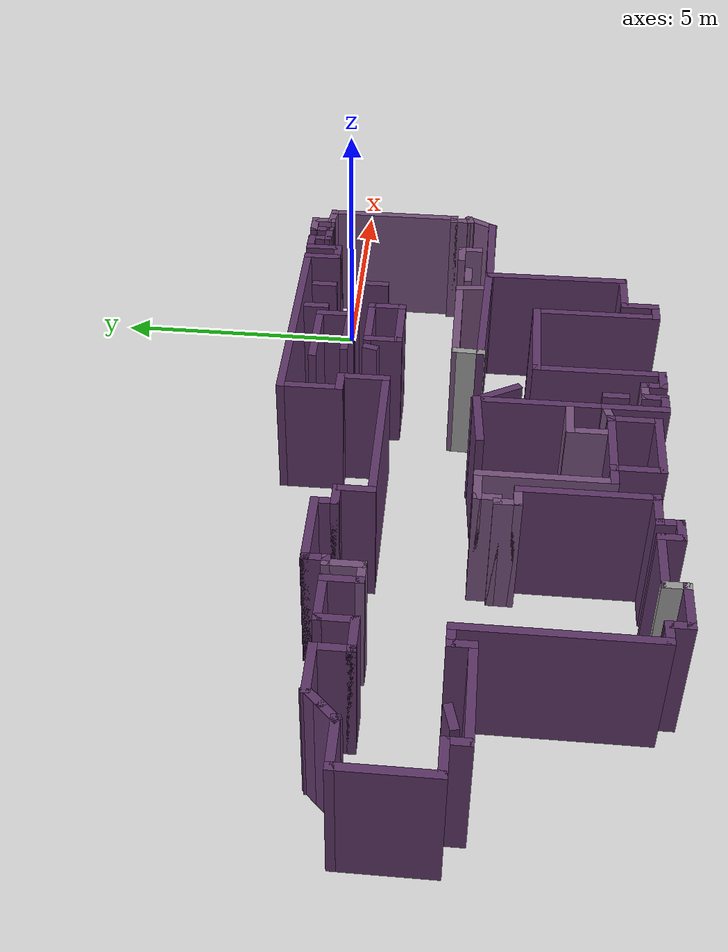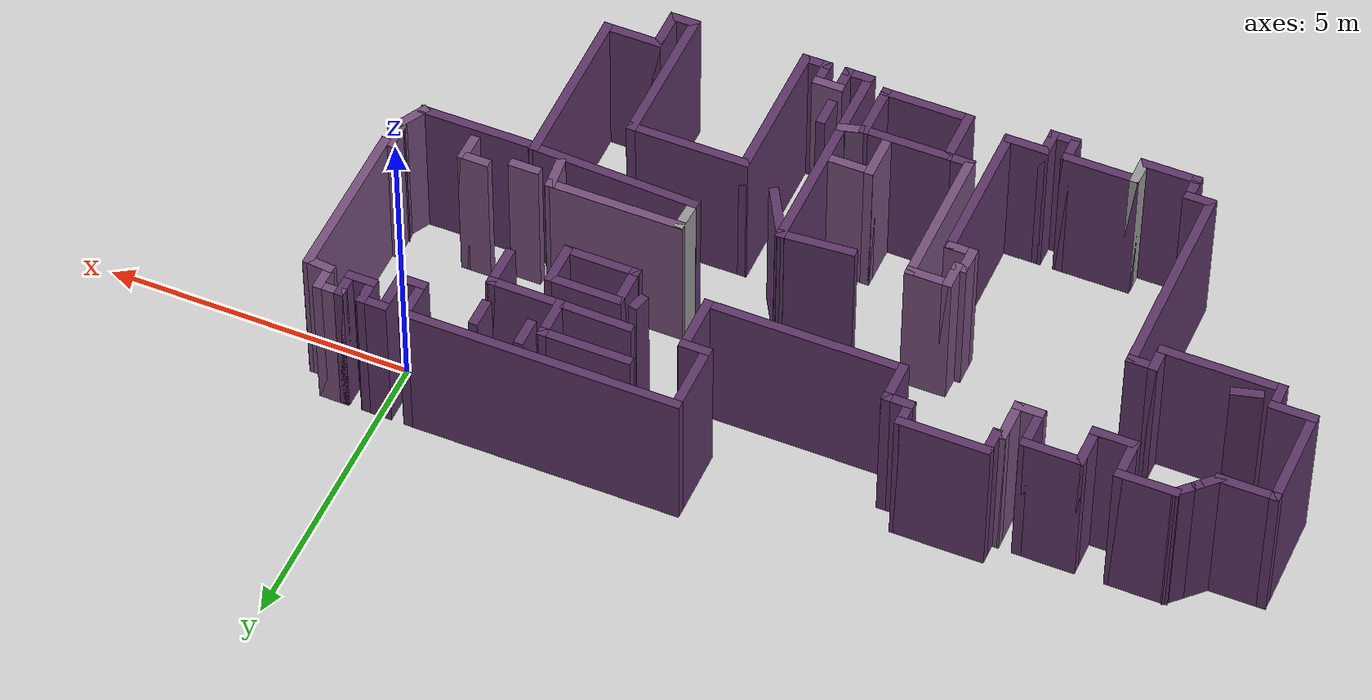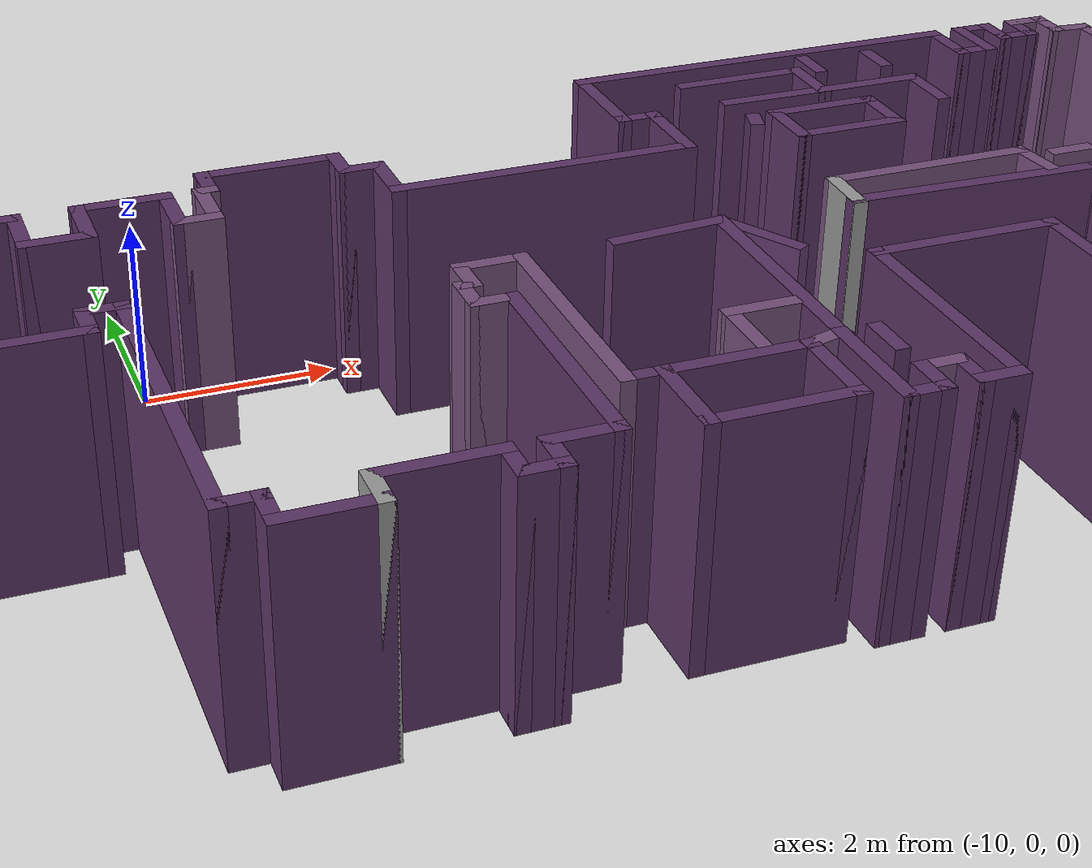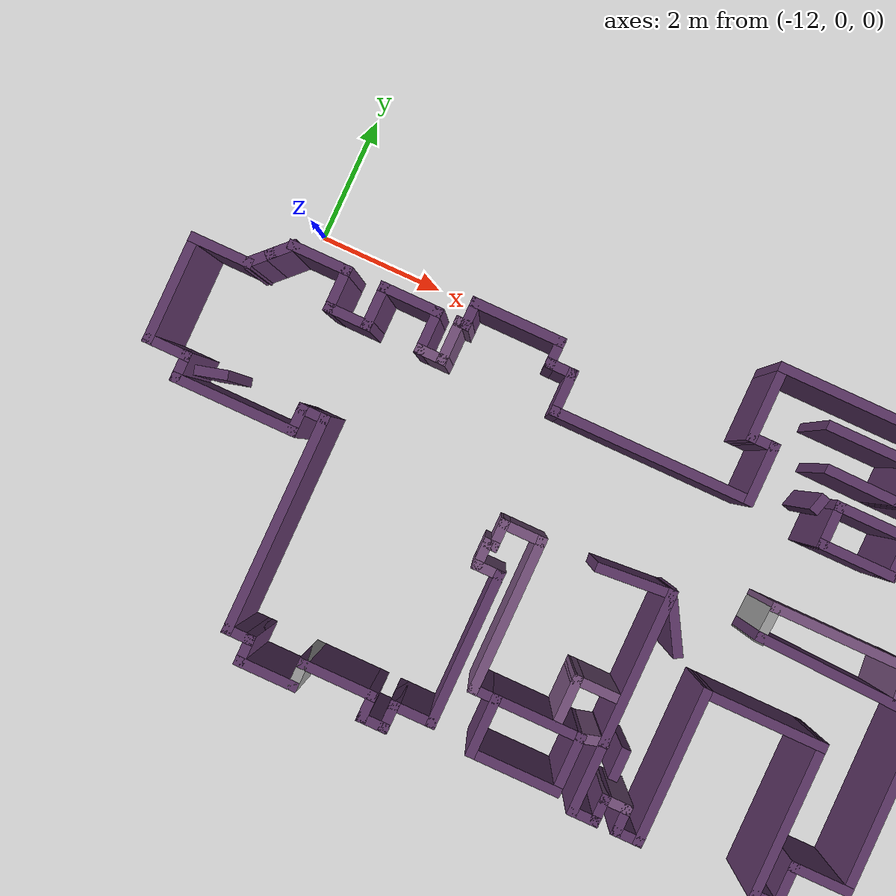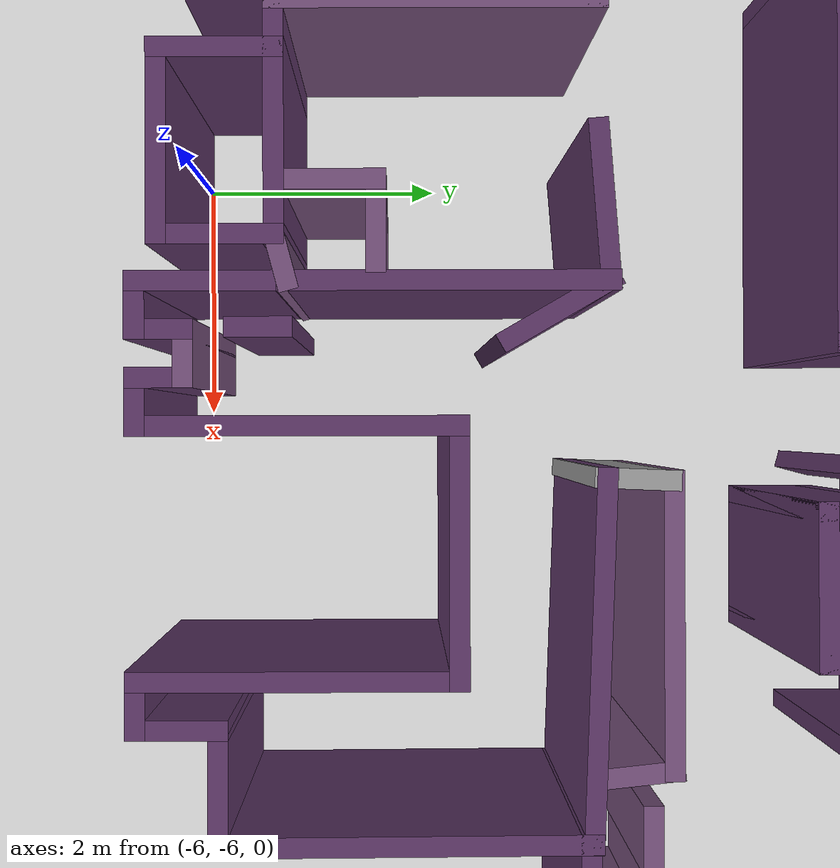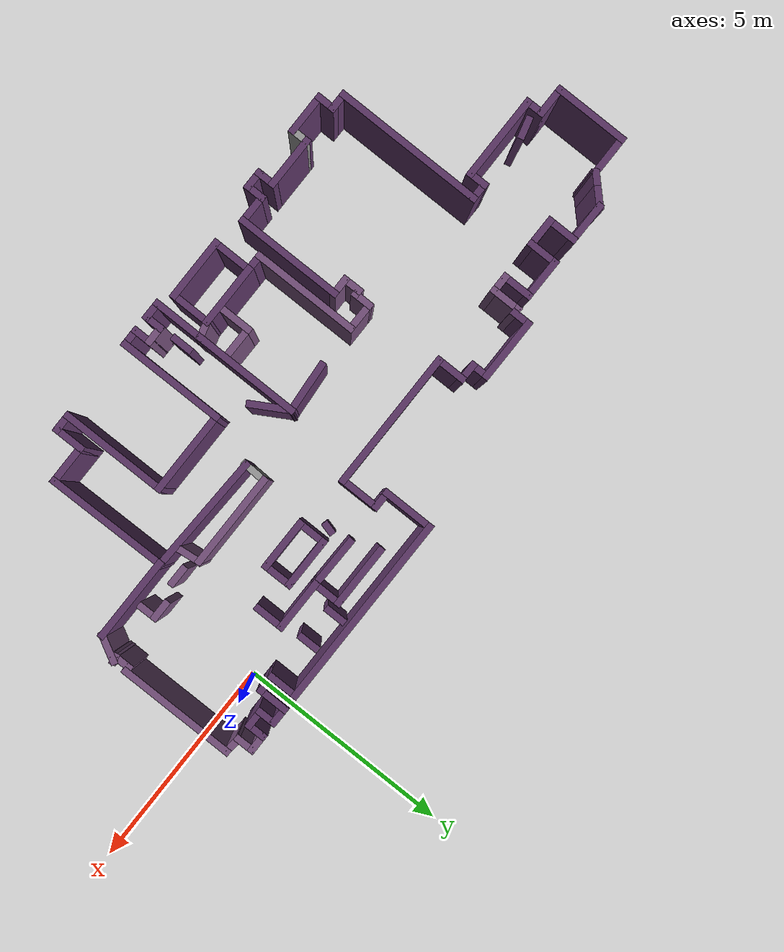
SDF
<?xml version='1.0'?>
<sdf version='1.6'>
  <model name='map_35'>
    <pose frame=''>-6.03093 -2.69462 0 0 -0 0</pose>
    <link name='Wall_0'>
      <collision name='Wall_0_Collision'>
        <geometry>
          <box>
            <size>4.5 0.15 2.5</size>
          </box>
        </geometry>
        <pose frame=''>0 0 1.25 0 -0 0</pose>
      </collision>
      <visual name='Wall_0_Visual'>
        <pose frame=''>0 0 1.25 0 -0 0</pose>
        <geometry>
          <box>
            <size>4.5 0.15 2.5</size>
          </box>
        </geometry>
        <material>
          <script>
            <uri>file://media/materials/scripts/gazebo.material</uri>
            <name>Gazebo/Grey</name>
          </script>
          <ambient>0.360784 0.207843 0.4 1</ambient>
        </material>
        <meta>
          <layer>0</layer>
        </meta>
      </visual>
      <pose frame=''>3.38761 3.57249 0 0 -0 3.14159</pose>
    </link>
    <link name='Wall_1'>
      <collision name='Wall_1_Collision'>
        <geometry>
          <box>
            <size>1.25 0.15 2.5</size>
          </box>
        </geometry>
        <pose frame=''>0 0 1.25 0 -0 0</pose>
      </collision>
      <visual name='Wall_1_Visual'>
        <pose frame=''>0 0 1.25 0 -0 0</pose>
        <geometry>
          <box>
            <size>1.25 0.15 2.5</size>
          </box>
        </geometry>
        <material>
          <script>
            <uri>file://media/materials/scripts/gazebo.material</uri>
            <name>Gazebo/Grey</name>
          </script>
          <ambient>0.360784 0.207843 0.4 1</ambient>
        </material>
        <meta>
          <layer>0</layer>
        </meta>
      </visual>
      <pose frame=''>1.21261 3.02249 0 0 -0 -1.5708</pose>
    </link>
    <link name='Wall_10'>
      <collision name='Wall_10_Collision'>
        <geometry>
          <box>
            <size>1.5 0.15 2.5</size>
          </box>
        </geometry>
        <pose frame=''>0 0 1.25 0 -0 0</pose>
      </collision>
      <visual name='Wall_10_Visual'>
        <pose frame=''>0 0 1.25 0 -0 0</pose>
        <geometry>
          <box>
            <size>1.5 0.15 2.5</size>
          </box>
        </geometry>
        <material>
          <script>
            <uri>file://media/materials/scripts/gazebo.material</uri>
            <name>Gazebo/Grey</name>
          </script>
          <ambient>0.360784 0.207843 0.4 1</ambient>
        </material>
        <meta>
          <layer>0</layer>
        </meta>
      </visual>
      <pose frame=''>-2.56239 2.57249 0 0 -0 3.14159</pose>
    </link>
    <link name='Wall_103'>
      <collision name='Wall_103_Collision'>
        <geometry>
          <box>
            <size>2 0.15 2.5</size>
          </box>
        </geometry>
        <pose frame=''>0 0 1.25 0 -0 0</pose>
      </collision>
      <visual name='Wall_103_Visual'>
        <pose frame=''>0 0 1.25 0 -0 0</pose>
        <geometry>
          <box>
            <size>2 0.15 2.5</size>
          </box>
        </geometry>
        <material>
          <script>
            <uri>file://media/materials/scripts/gazebo.material</uri>
            <name>Gazebo/Grey</name>
          </script>
          <ambient>0.360784 0.207843 0.4 1</ambient>
        </material>
        <meta>
          <layer>0</layer>
        </meta>
      </visual>
      <pose frame=''>6.1106 -0.231333 0 0 -0 0</pose>
    </link>
    <link name='Wall_104'>
      <collision name='Wall_104_Collision'>
        <geometry>
          <box>
            <size>0.717797 0.15 2.5</size>
          </box>
        </geometry>
        <pose frame=''>0 0 1.25 0 -0 0</pose>
      </collision>
      <visual name='Wall_104_Visual'>
        <pose frame=''>0 0 1.25 0 -0 0</pose>
        <geometry>
          <box>
            <size>0.717797 0.15 2.5</size>
          </box>
        </geometry>
        <material>
          <script>
            <uri>file://media/materials/scripts/gazebo.material</uri>
            <name>Gazebo/Grey</name>
          </script>
          <ambient>0.458824 0.313726 0.482353 1</ambient>
        </material>
        <meta>
          <layer>0</layer>
        </meta>
      </visual>
      <pose frame=''>7.17066 0.018383 0 0 -0 1.07501</pose>
    </link>
    <link name='Wall_105'>
      <collision name='Wall_105_Collision'>
        <geometry>
          <box>
            <size>0.25 0.15 2.5</size>
          </box>
        </geometry>
        <pose frame=''>0 0 1.25 0 -0 0</pose>
      </collision>
      <visual name='Wall_105_Visual'>
        <pose frame=''>0 0 1.25 0 -0 0</pose>
        <geometry>
          <box>
            <size>0.25 0.15 2.5</size>
          </box>
        </geometry>
        <material>
          <script>
            <uri>file://media/materials/scripts/gazebo.material</uri>
            <name>Gazebo/Grey</name>
          </script>
          <ambient>0.458824 0.313726 0.482353 1</ambient>
        </material>
        <meta>
          <layer>0</layer>
        </meta>
      </visual>
      <pose frame=''>7.25742 0.255158 0 0 -0 -2.87979</pose>
    </link>
    <link name='Wall_106'>
      <collision name='Wall_106_Collision'>
        <geometry>
          <box>
            <size>0.5 0.15 2.5</size>
          </box>
        </geometry>
        <pose frame=''>0 0 1.25 0 -0 0</pose>
      </collision>
      <visual name='Wall_106_Visual'>
        <pose frame=''>0 0 1.25 0 -0 0</pose>
        <geometry>
          <box>
            <size>0.5 0.15 2.5</size>
          </box>
        </geometry>
        <material>
          <script>
            <uri>file://media/materials/scripts/gazebo.material</uri>
            <name>Gazebo/Grey</name>
          </script>
          <ambient>0.458824 0.313726 0.482353 1</ambient>
        </material>
        <meta>
          <layer>0</layer>
        </meta>
      </visual>
      <pose frame=''>7.20912 0.417217 0 0 -0 1.5708</pose>
    </link>
    <link name='Wall_107'>
      <collision name='Wall_107_Collision'>
        <geometry>
          <box>
            <size>0.25 0.15 2.5</size>
          </box>
        </geometry>
        <pose frame=''>0 0 1.25 0 -0 0</pose>
      </collision>
      <visual name='Wall_107_Visual'>
        <pose frame=''>0 0 1.25 0 -0 0</pose>
        <geometry>
          <box>
            <size>0.25 0.15 2.5</size>
          </box>
        </geometry>
        <material>
          <script>
            <uri>file://media/materials/scripts/gazebo.material</uri>
            <name>Gazebo/Grey</name>
          </script>
          <ambient>0.458824 0.313726 0.482353 1</ambient>
        </material>
        <meta>
          <layer>0</layer>
        </meta>
      </visual>
      <pose frame=''>7.25912 0.592217 0 0 -0 0</pose>
    </link>
    <link name='Wall_108'>
      <collision name='Wall_108_Collision'>
        <geometry>
          <box>
            <size>2.75 0.15 2.5</size>
          </box>
        </geometry>
        <pose frame=''>0 0 1.25 0 -0 0</pose>
      </collision>
      <visual name='Wall_108_Visual'>
        <pose frame=''>0 0 1.25 0 -0 0</pose>
        <geometry>
          <box>
            <size>2.75 0.15 2.5</size>
          </box>
        </geometry>
        <material>
          <script>
            <uri>file://media/materials/scripts/gazebo.material</uri>
            <name>Gazebo/Grey</name>
          </script>
          <ambient>0.458824 0.313726 0.482353 1</ambient>
        </material>
        <meta>
          <layer>0</layer>
        </meta>
      </visual>
      <pose frame=''>7.30912 1.89222 0 0 -0 1.5708</pose>
    </link>
    <link name='Wall_11'>
      <collision name='Wall_11_Collision'>
        <geometry>
          <box>
            <size>0.5 0.15 2.5</size>
          </box>
        </geometry>
        <pose frame=''>0 0 1.25 0 -0 0</pose>
      </collision>
      <visual name='Wall_11_Visual'>
        <pose frame=''>0 0 1.25 0 -0 0</pose>
        <geometry>
          <box>
            <size>0.5 0.15 2.5</size>
          </box>
        </geometry>
        <material>
          <script>
            <uri>file://media/materials/scripts/gazebo.material</uri>
            <name>Gazebo/Grey</name>
          </script>
          <ambient>0.360784 0.207843 0.4 1</ambient>
        </material>
        <meta>
          <layer>0</layer>
        </meta>
      </visual>
      <pose frame=''>-3.23739 2.39749 0 0 -0 -1.5708</pose>
    </link>
    <link name='Wall_115'>
      <collision name='Wall_115_Collision'>
        <geometry>
          <box>
            <size>0.75 0.15 2.5</size>
          </box>
        </geometry>
        <pose frame=''>0 0 1.25 0 -0 0</pose>
      </collision>
      <visual name='Wall_115_Visual'>
        <pose frame=''>0 0 1.25 0 -0 0</pose>
        <geometry>
          <box>
            <size>0.75 0.15 2.5</size>
          </box>
        </geometry>
        <material>
          <script>
            <uri>file://media/materials/scripts/gazebo.material</uri>
            <name>Gazebo/Grey</name>
          </script>
          <ambient>0.360784 0.207843 0.4 1</ambient>
        </material>
        <meta>
          <layer>0</layer>
        </meta>
      </visual>
      <pose frame=''>5.56261 3.27249 0 0 -0 -1.5708</pose>
    </link>
    <link name='Wall_116'>
      <collision name='Wall_116_Collision'>
        <geometry>
          <box>
            <size>0.5 0.15 2.5</size>
          </box>
        </geometry>
        <pose frame=''>0 0 1.25 0 -0 0</pose>
      </collision>
      <visual name='Wall_116_Visual'>
        <pose frame=''>0 0 1.25 0 -0 0</pose>
        <geometry>
          <box>
            <size>0.5 0.15 2.5</size>
          </box>
        </geometry>
        <material>
          <script>
            <uri>file://media/materials/scripts/gazebo.material</uri>
            <name>Gazebo/Grey</name>
          </script>
          <ambient>0.360784 0.207843 0.4 1</ambient>
        </material>
        <meta>
          <layer>0</layer>
        </meta>
      </visual>
      <pose frame=''>5.73761 2.97249 0 0 -0 0</pose>
    </link>
    <link name='Wall_119'>
      <collision name='Wall_119_Collision'>
        <geometry>
          <box>
            <size>0.75 0.15 2.5</size>
          </box>
        </geometry>
        <pose frame=''>0 0 1.25 0 -0 0</pose>
      </collision>
      <visual name='Wall_119_Visual'>
        <pose frame=''>0 0 1.25 0 -0 0</pose>
        <geometry>
          <box>
            <size>0.75 0.15 2.5</size>
          </box>
        </geometry>
        <material>
          <script>
            <uri>file://media/materials/scripts/gazebo.material</uri>
            <name>Gazebo/Grey</name>
          </script>
          <ambient>0.360784 0.207843 0.4 1</ambient>
        </material>
        <meta>
          <layer>0</layer>
        </meta>
      </visual>
      <pose frame=''>5.91261 3.27249 0 0 -0 1.5708</pose>
    </link>
    <link name='Wall_12'>
      <collision name='Wall_12_Collision'>
        <geometry>
          <box>
            <size>0.25 0.15 2.5</size>
          </box>
        </geometry>
        <pose frame=''>0 0 1.25 0 -0 0</pose>
      </collision>
      <visual name='Wall_12_Visual'>
        <pose frame=''>0 0 1.25 0 -0 0</pose>
        <geometry>
          <box>
            <size>0.25 0.15 2.5</size>
          </box>
        </geometry>
        <material>
          <script>
            <uri>file://media/materials/scripts/gazebo.material</uri>
            <name>Gazebo/Grey</name>
          </script>
          <ambient>0.458824 0.313726 0.482353 1</ambient>
        </material>
        <meta>
          <layer>0</layer>
        </meta>
      </visual>
      <pose frame=''>-3.28739 2.22249 0 0 -0 3.14159</pose>
    </link>
    <link name='Wall_120'>
      <collision name='Wall_120_Collision'>
        <geometry>
          <box>
            <size>0.5 0.15 2.5</size>
          </box>
        </geometry>
        <pose frame=''>0 0 1.25 0 -0 0</pose>
      </collision>
      <visual name='Wall_120_Visual'>
        <pose frame=''>0 0 1.25 0 -0 0</pose>
        <geometry>
          <box>
            <size>0.5 0.15 2.5</size>
          </box>
        </geometry>
        <material>
          <script>
            <uri>file://media/materials/scripts/gazebo.material</uri>
            <name>Gazebo/Grey</name>
          </script>
          <ambient>0.360784 0.207843 0.4 1</ambient>
        </material>
        <meta>
          <layer>0</layer>
        </meta>
      </visual>
      <pose frame=''>6.08761 3.57249 0 0 -0 0</pose>
    </link>
    <link name='Wall_121'>
      <collision name='Wall_121_Collision'>
        <geometry>
          <box>
            <size>0.5 0.15 2.5</size>
          </box>
        </geometry>
        <pose frame=''>0 0 1.25 0 -0 0</pose>
      </collision>
      <visual name='Wall_121_Visual'>
        <pose frame=''>0 0 1.25 0 -0 0</pose>
        <geometry>
          <box>
            <size>0.5 0.15 2.5</size>
          </box>
        </geometry>
        <material>
          <script>
            <uri>file://media/materials/scripts/gazebo.material</uri>
            <name>Gazebo/Grey</name>
          </script>
          <ambient>0.360784 0.207843 0.4 1</ambient>
        </material>
        <meta>
          <layer>0</layer>
        </meta>
      </visual>
      <pose frame=''>6.26261 3.39749 0 0 -0 -1.5708</pose>
    </link>
    <link name='Wall_122'>
      <collision name='Wall_122_Collision'>
        <geometry>
          <box>
            <size>0.5 0.15 2.5</size>
          </box>
        </geometry>
        <pose frame=''>0 0 1.25 0 -0 0</pose>
      </collision>
      <visual name='Wall_122_Visual'>
        <pose frame=''>0 0 1.25 0 -0 0</pose>
        <geometry>
          <box>
            <size>0.5 0.15 2.5</size>
          </box>
        </geometry>
        <material>
          <script>
            <uri>file://media/materials/scripts/gazebo.material</uri>
            <name>Gazebo/Grey</name>
          </script>
          <ambient>0.360784 0.207843 0.4 1</ambient>
        </material>
        <meta>
          <layer>0</layer>
        </meta>
      </visual>
      <pose frame=''>6.43761 3.22249 0 0 -0 0</pose>
    </link>
    <link name='Wall_123'>
      <collision name='Wall_123_Collision'>
        <geometry>
          <box>
            <size>0.5 0.15 2.5</size>
          </box>
        </geometry>
        <pose frame=''>0 0 1.25 0 -0 0</pose>
      </collision>
      <visual name='Wall_123_Visual'>
        <pose frame=''>0 0 1.25 0 -0 0</pose>
        <geometry>
          <box>
            <size>0.5 0.15 2.5</size>
          </box>
        </geometry>
        <material>
          <script>
            <uri>file://media/materials/scripts/gazebo.material</uri>
            <name>Gazebo/Grey</name>
          </script>
          <ambient>0.360784 0.207843 0.4 1</ambient>
        </material>
        <meta>
          <layer>0</layer>
        </meta>
      </visual>
      <pose frame=''>6.61261 3.39749 0 0 -0 1.5708</pose>
    </link>
    <link name='Wall_124'>
      <collision name='Wall_124_Collision'>
        <geometry>
          <box>
            <size>0.5 0.15 2.5</size>
          </box>
        </geometry>
        <pose frame=''>0 0 1.25 0 -0 0</pose>
      </collision>
      <visual name='Wall_124_Visual'>
        <pose frame=''>0 0 1.25 0 -0 0</pose>
        <geometry>
          <box>
            <size>0.5 0.15 2.5</size>
          </box>
        </geometry>
        <material>
          <script>
            <uri>file://media/materials/scripts/gazebo.material</uri>
            <name>Gazebo/Grey</name>
          </script>
          <ambient>0.458824 0.313726 0.482353 1</ambient>
        </material>
        <meta>
          <layer>0</layer>
        </meta>
      </visual>
      <pose frame=''>6.78761 3.57249 0 0 -0 0</pose>
    </link>
    <link name='Wall_125'>
      <collision name='Wall_125_Collision'>
        <geometry>
          <box>
            <size>0.5 0.15 2.5</size>
          </box>
        </geometry>
        <pose frame=''>0 0 1.25 0 -0 0</pose>
      </collision>
      <visual name='Wall_125_Visual'>
        <pose frame=''>0 0 1.25 0 -0 0</pose>
        <geometry>
          <box>
            <size>0.5 0.15 2.5</size>
          </box>
        </geometry>
        <material>
          <script>
            <uri>file://media/materials/scripts/gazebo.material</uri>
            <name>Gazebo/Grey</name>
          </script>
          <ambient>0.458824 0.313726 0.482353 1</ambient>
        </material>
        <meta>
          <layer>0</layer>
        </meta>
      </visual>
      <pose frame=''>6.96261 3.39749 0 0 -0 -1.5708</pose>
    </link>
    <link name='Wall_126'>
      <collision name='Wall_126_Collision'>
        <geometry>
          <box>
            <size>0.497826 0.15 2.5</size>
          </box>
        </geometry>
        <pose frame=''>0 0 1.25 0 -0 0</pose>
      </collision>
      <visual name='Wall_126_Visual'>
        <pose frame=''>0 0 1.25 0 -0 0</pose>
        <geometry>
          <box>
            <size>0.497826 0.15 2.5</size>
          </box>
        </geometry>
        <material>
          <script>
            <uri>file://media/materials/scripts/gazebo.material</uri>
            <name>Gazebo/Grey</name>
          </script>
          <ambient>0.458824 0.313726 0.482353 1</ambient>
        </material>
        <meta>
          <layer>0</layer>
        </meta>
      </visual>
      <pose frame=''>7.13587 3.20735 0 0 -0 -0.087136</pose>
    </link>
    <link name='Wall_128'>
      <collision name='Wall_128_Collision'>
        <geometry>
          <box>
            <size>0.75 0.15 2.5</size>
          </box>
        </geometry>
        <pose frame=''>0 0 1.25 0 -0 0</pose>
      </collision>
      <visual name='Wall_128_Visual'>
        <pose frame=''>0 0 1.25 0 -0 0</pose>
        <geometry>
          <box>
            <size>0.75 0.15 2.5</size>
          </box>
        </geometry>
        <material>
          <script>
            <uri>file://media/materials/scripts/gazebo.material</uri>
            <name>Gazebo/Grey</name>
          </script>
          <ambient>0.360784 0.207843 0.4 1</ambient>
        </material>
        <meta>
          <layer>0</layer>
        </meta>
      </visual>
      <pose frame=''>2.78694 1.78408 0 0 -0 -1.5708</pose>
    </link>
    <link name='Wall_129'>
      <collision name='Wall_129_Collision'>
        <geometry>
          <box>
            <size>1.25 0.15 2.5</size>
          </box>
        </geometry>
        <pose frame=''>0 0 1.25 0 -0 0</pose>
      </collision>
      <visual name='Wall_129_Visual'>
        <pose frame=''>0 0 1.25 0 -0 0</pose>
        <geometry>
          <box>
            <size>1.25 0.15 2.5</size>
          </box>
        </geometry>
        <material>
          <script>
            <uri>file://media/materials/scripts/gazebo.material</uri>
            <name>Gazebo/Grey</name>
          </script>
          <ambient>0.360784 0.207843 0.4 1</ambient>
        </material>
        <meta>
          <layer>0</layer>
        </meta>
      </visual>
      <pose frame=''>3.33694 1.48408 0 0 -0 0</pose>
    </link>
    <link name='Wall_13'>
      <collision name='Wall_13_Collision'>
        <geometry>
          <box>
            <size>0.75 0.15 2.5</size>
          </box>
        </geometry>
        <pose frame=''>0 0 1.25 0 -0 0</pose>
      </collision>
      <visual name='Wall_13_Visual'>
        <pose frame=''>0 0 1.25 0 -0 0</pose>
        <geometry>
          <box>
            <size>0.75 0.15 2.5</size>
          </box>
        </geometry>
        <material>
          <script>
            <uri>file://media/materials/scripts/gazebo.material</uri>
            <name>Gazebo/Grey</name>
          </script>
          <ambient>0.458824 0.313726 0.482353 1</ambient>
        </material>
        <meta>
          <layer>0</layer>
        </meta>
      </visual>
      <pose frame=''>-3.33739 1.92249 0 0 -0 -1.5708</pose>
    </link>
    <link name='Wall_130'>
      <collision name='Wall_130_Collision'>
        <geometry>
          <box>
            <size>0.75 0.15 2.5</size>
          </box>
        </geometry>
        <pose frame=''>0 0 1.25 0 -0 0</pose>
      </collision>
      <visual name='Wall_130_Visual'>
        <pose frame=''>0 0 1.25 0 -0 0</pose>
        <geometry>
          <box>
            <size>0.75 0.15 2.5</size>
          </box>
        </geometry>
        <material>
          <script>
            <uri>file://media/materials/scripts/gazebo.material</uri>
            <name>Gazebo/Grey</name>
          </script>
          <ambient>0.360784 0.207843 0.4 1</ambient>
        </material>
        <meta>
          <layer>0</layer>
        </meta>
      </visual>
      <pose frame=''>3.88694 1.78408 0 0 -0 1.5708</pose>
    </link>
    <link name='Wall_131'>
      <collision name='Wall_131_Collision'>
        <geometry>
          <box>
            <size>1.25 0.15 2.5</size>
          </box>
        </geometry>
        <pose frame=''>0 0 1.25 0 -0 0</pose>
      </collision>
      <visual name='Wall_131_Visual'>
        <pose frame=''>0 0 1.25 0 -0 0</pose>
        <geometry>
          <box>
            <size>1.25 0.15 2.5</size>
          </box>
        </geometry>
        <material>
          <script>
            <uri>file://media/materials/scripts/gazebo.material</uri>
            <name>Gazebo/Grey</name>
          </script>
          <ambient>0.360784 0.207843 0.4 1</ambient>
        </material>
        <meta>
          <layer>0</layer>
        </meta>
      </visual>
      <pose frame=''>3.33694 2.08408 0 0 -0 3.14159</pose>
    </link>
    <link name='Wall_133'>
      <collision name='Wall_133_Collision'>
        <geometry>
          <box>
            <size>0.3 0.15 2.5</size>
          </box>
        </geometry>
        <pose frame=''>0 0 1.25 0 -0 0</pose>
      </collision>
      <visual name='Wall_133_Visual'>
        <pose frame=''>0 0 1.25 0 -0 0</pose>
        <geometry>
          <box>
            <size>0.3 0.15 2.5</size>
          </box>
        </geometry>
        <material>
          <script>
            <uri>file://media/materials/scripts/gazebo.material</uri>
            <name>Gazebo/Grey</name>
          </script>
          <ambient>0.360784 0.207843 0.4 1</ambient>
        </material>
        <meta>
          <layer>0</layer>
        </meta>
      </visual>
      <pose frame=''>2.50465 1.99562 0 0 -0 1.309</pose>
    </link>
    <link name='Wall_135'>
      <collision name='Wall_135_Collision'>
        <geometry>
          <box>
            <size>1.5 0.15 2.5</size>
          </box>
        </geometry>
        <pose frame=''>0 0 1.25 0 -0 0</pose>
      </collision>
      <visual name='Wall_135_Visual'>
        <pose frame=''>0 0 1.25 0 -0 0</pose>
        <geometry>
          <box>
            <size>1.5 0.15 2.5</size>
          </box>
        </geometry>
        <material>
          <script>
            <uri>file://media/materials/scripts/gazebo.material</uri>
            <name>Gazebo/Grey</name>
          </script>
          <ambient>0.360784 0.207843 0.4 1</ambient>
        </material>
        <meta>
          <layer>0</layer>
        </meta>
      </visual>
      <pose frame=''>2.87865 3.08976 0 0 -0 0</pose>
    </link>
    <link name='Wall_136'>
      <collision name='Wall_136_Collision'>
        <geometry>
          <box>
            <size>0.75 0.15 2.5</size>
          </box>
        </geometry>
        <pose frame=''>0 0 1.25 0 -0 0</pose>
      </collision>
      <visual name='Wall_136_Visual'>
        <pose frame=''>0 0 1.25 0 -0 0</pose>
        <geometry>
          <box>
            <size>0.75 0.15 2.5</size>
          </box>
        </geometry>
        <material>
          <script>
            <uri>file://media/materials/scripts/gazebo.material</uri>
            <name>Gazebo/Grey</name>
          </script>
          <ambient>0.360784 0.207843 0.4 1</ambient>
        </material>
        <meta>
          <layer>0</layer>
        </meta>
      </visual>
      <pose frame=''>3.55365 2.78976 0 0 -0 -1.5708</pose>
    </link>
    <link name='Wall_137'>
      <collision name='Wall_137_Collision'>
        <geometry>
          <box>
            <size>1.25 0.15 2.5</size>
          </box>
        </geometry>
        <pose frame=''>0 0 1.25 0 -0 0</pose>
      </collision>
      <visual name='Wall_137_Visual'>
        <pose frame=''>0 0 1.25 0 -0 0</pose>
        <geometry>
          <box>
            <size>1.25 0.15 2.5</size>
          </box>
        </geometry>
        <material>
          <script>
            <uri>file://media/materials/scripts/gazebo.material</uri>
            <name>Gazebo/Grey</name>
          </script>
          <ambient>0.360784 0.207843 0.4 1</ambient>
        </material>
        <meta>
          <layer>0</layer>
        </meta>
      </visual>
      <pose frame=''>4.10365 2.48976 0 0 -0 0</pose>
    </link>
    <link name='Wall_138'>
      <collision name='Wall_138_Collision'>
        <geometry>
          <box>
            <size>0.75 0.15 2.5</size>
          </box>
        </geometry>
        <pose frame=''>0 0 1.25 0 -0 0</pose>
      </collision>
      <visual name='Wall_138_Visual'>
        <pose frame=''>0 0 1.25 0 -0 0</pose>
        <geometry>
          <box>
            <size>0.75 0.15 2.5</size>
          </box>
        </geometry>
        <material>
          <script>
            <uri>file://media/materials/scripts/gazebo.material</uri>
            <name>Gazebo/Grey</name>
          </script>
          <ambient>0.360784 0.207843 0.4 1</ambient>
        </material>
        <meta>
          <layer>0</layer>
        </meta>
      </visual>
      <pose frame=''>4.65365 2.18976 0 0 -0 -1.5708</pose>
    </link>
    <link name='Wall_14'>
      <collision name='Wall_14_Collision'>
        <geometry>
          <box>
            <size>0.5 0.15 2.5</size>
          </box>
        </geometry>
        <pose frame=''>0 0 1.25 0 -0 0</pose>
      </collision>
      <visual name='Wall_14_Visual'>
        <pose frame=''>0 0 1.25 0 -0 0</pose>
        <geometry>
          <box>
            <size>0.5 0.15 2.5</size>
          </box>
        </geometry>
        <material>
          <script>
            <uri>file://media/materials/scripts/gazebo.material</uri>
            <name>Gazebo/Grey</name>
          </script>
          <ambient>0.458824 0.313726 0.482353 1</ambient>
        </material>
        <meta>
          <layer>0</layer>
        </meta>
      </visual>
      <pose frame=''>-3.51239 1.62249 0 0 -0 3.14159</pose>
    </link>
    <link name='Wall_140'>
      <collision name='Wall_140_Collision'>
        <geometry>
          <box>
            <size>1.25876 0.15 2.5</size>
          </box>
        </geometry>
        <pose frame=''>0 0 1.25 0 -0 0</pose>
      </collision>
      <visual name='Wall_140_Visual'>
        <pose frame=''>0 0 1.25 0 -0 0</pose>
        <geometry>
          <box>
            <size>1.25876 0.15 2.5</size>
          </box>
        </geometry>
        <material>
          <script>
            <uri>file://media/materials/scripts/gazebo.material</uri>
            <name>Gazebo/Grey</name>
          </script>
          <ambient>0.360784 0.207843 0.4 1</ambient>
        </material>
        <meta>
          <layer>0</layer>
        </meta>
      </visual>
      <pose frame=''>2.99933 2.49811 0 0 -0 -0.015068</pose>
    </link>
    <link name='Wall_142'>
      <collision name='Wall_142_Collision'>
        <geometry>
          <box>
            <size>0.5 0.15 2.5</size>
          </box>
        </geometry>
        <pose frame=''>0 0 1.25 0 -0 0</pose>
      </collision>
      <visual name='Wall_142_Visual'>
        <pose frame=''>0 0 1.25 0 -0 0</pose>
        <geometry>
          <box>
            <size>0.5 0.15 2.5</size>
          </box>
        </geometry>
        <material>
          <script>
            <uri>file://media/materials/scripts/gazebo.material</uri>
            <name>Gazebo/Grey</name>
          </script>
          <ambient>0.360784 0.207843 0.4 1</ambient>
        </material>
        <meta>
          <layer>0</layer>
        </meta>
      </visual>
      <pose frame=''>3.79262 3.19635 0 0 -0 -1.5708</pose>
    </link>
    <link name='Wall_144'>
      <collision name='Wall_144_Collision'>
        <geometry>
          <box>
            <size>0.5 0.15 2.5</size>
          </box>
        </geometry>
        <pose frame=''>0 0 1.25 0 -0 0</pose>
      </collision>
      <visual name='Wall_144_Visual'>
        <pose frame=''>0 0 1.25 0 -0 0</pose>
        <geometry>
          <box>
            <size>0.5 0.15 2.5</size>
          </box>
        </geometry>
        <material>
          <script>
            <uri>file://media/materials/scripts/gazebo.material</uri>
            <name>Gazebo/Grey</name>
          </script>
          <ambient>0.360784 0.207843 0.4 1</ambient>
        </material>
        <meta>
          <layer>0</layer>
        </meta>
      </visual>
      <pose frame=''>4.55693 3.1159 0 0 -0 -1.5708</pose>
    </link>
    <link name='Wall_146'>
      <collision name='Wall_146_Collision'>
        <geometry>
          <box>
            <size>0.5 0.15 2.5</size>
          </box>
        </geometry>
        <pose frame=''>0 0 1.25 0 -0 0</pose>
      </collision>
      <visual name='Wall_146_Visual'>
        <pose frame=''>0 0 1.25 0 -0 0</pose>
        <geometry>
          <box>
            <size>0.5 0.15 2.5</size>
          </box>
        </geometry>
        <material>
          <script>
            <uri>file://media/materials/scripts/gazebo.material</uri>
            <name>Gazebo/Grey</name>
          </script>
          <ambient>0.458824 0.313726 0.482353 1</ambient>
        </material>
        <meta>
          <layer>0</layer>
        </meta>
      </visual>
      <pose frame=''>5.15432 0.213521 0 0 -0 0</pose>
    </link>
    <link name='Wall_150'>
      <collision name='Wall_150_Collision'>
        <geometry>
          <box>
            <size>0.5 0.15 2.5</size>
          </box>
        </geometry>
        <pose frame=''>0 0 1.25 0 -0 0</pose>
      </collision>
      <visual name='Wall_150_Visual'>
        <pose frame=''>0 0 1.25 0 -0 0</pose>
        <geometry>
          <box>
            <size>0.5 0.15 2.5</size>
          </box>
        </geometry>
        <material>
          <script>
            <uri>file://media/materials/scripts/gazebo.material</uri>
            <name>Gazebo/Grey</name>
          </script>
          <ambient>0.458824 0.313726 0.482353 1</ambient>
        </material>
        <meta>
          <layer>0</layer>
        </meta>
      </visual>
      <pose frame=''>5.91864 0.37443 0 0 -0 0</pose>
    </link>
    <link name='Wall_151'>
      <collision name='Wall_151_Collision'>
        <geometry>
          <box>
            <size>0.5 0.15 2.5</size>
          </box>
        </geometry>
        <pose frame=''>0 0 1.25 0 -0 0</pose>
      </collision>
      <visual name='Wall_151_Visual'>
        <pose frame=''>0 0 1.25 0 -0 0</pose>
        <geometry>
          <box>
            <size>0.5 0.15 2.5</size>
          </box>
        </geometry>
        <material>
          <script>
            <uri>file://media/materials/scripts/gazebo.material</uri>
            <name>Gazebo/Grey</name>
          </script>
          <ambient>0.458824 0.313726 0.482353 1</ambient>
        </material>
        <meta>
          <layer>0</layer>
        </meta>
      </visual>
      <pose frame=''>6.09363 0.199429 0 0 -0 -1.5708</pose>
    </link>
    <link name='Wall_153'>
      <collision name='Wall_153_Collision'>
        <geometry>
          <box>
            <size>0.5 0.15 2.5</size>
          </box>
        </geometry>
        <pose frame=''>0 0 1.25 0 -0 0</pose>
      </collision>
      <visual name='Wall_153_Visual'>
        <pose frame=''>0 0 1.25 0 -0 0</pose>
        <geometry>
          <box>
            <size>0.5 0.15 2.5</size>
          </box>
        </geometry>
        <material>
          <script>
            <uri>file://media/materials/scripts/gazebo.material</uri>
            <name>Gazebo/Grey</name>
          </script>
          <ambient>0.360784 0.207843 0.4 1</ambient>
        </material>
        <meta>
          <layer>0</layer>
        </meta>
      </visual>
      <pose frame=''>1.43933 -2.63658 0 0 -0 -1.5708</pose>
    </link>
    <link name='Wall_155'>
      <collision name='Wall_155_Collision'>
        <geometry>
          <box>
            <size>0.5 0.15 2.5</size>
          </box>
        </geometry>
        <pose frame=''>0 0 1.25 0 -0 0</pose>
      </collision>
      <visual name='Wall_155_Visual'>
        <pose frame=''>0 0 1.25 0 -0 0</pose>
        <geometry>
          <box>
            <size>0.5 0.15 2.5</size>
          </box>
        </geometry>
        <material>
          <script>
            <uri>file://media/materials/scripts/gazebo.material</uri>
            <name>Gazebo/Grey</name>
          </script>
          <ambient>0.360784 0.207843 0.4 1</ambient>
        </material>
        <meta>
          <layer>0</layer>
        </meta>
      </visual>
      <pose frame=''>-6.29627 0.057679 0 0 -0 0.261799</pose>
    </link>
    <link name='Wall_17'>
      <collision name='Wall_17_Collision'>
        <geometry>
          <box>
            <size>0.75 0.15 2.5</size>
          </box>
        </geometry>
        <pose frame=''>0 0 1.25 0 -0 0</pose>
      </collision>
      <visual name='Wall_17_Visual'>
        <pose frame=''>0 0 1.25 0 -0 0</pose>
        <geometry>
          <box>
            <size>0.75 0.15 2.5</size>
          </box>
        </geometry>
        <material>
          <script>
            <uri>file://media/materials/scripts/gazebo.material</uri>
            <name>Gazebo/Grey</name>
          </script>
          <ambient>0.360784 0.207843 0.4 1</ambient>
        </material>
        <meta>
          <layer>0</layer>
        </meta>
      </visual>
      <pose frame=''>-3.68739 1.92249 0 0 -0 1.5708</pose>
    </link>
    <link name='Wall_18'>
      <collision name='Wall_18_Collision'>
        <geometry>
          <box>
            <size>1 0.15 2.5</size>
          </box>
        </geometry>
        <pose frame=''>0 0 1.25 0 -0 0</pose>
      </collision>
      <visual name='Wall_18_Visual'>
        <pose frame=''>0 0 1.25 0 -0 0</pose>
        <geometry>
          <box>
            <size>1 0.15 2.5</size>
          </box>
        </geometry>
        <material>
          <script>
            <uri>file://media/materials/scripts/gazebo.material</uri>
            <name>Gazebo/Grey</name>
          </script>
          <ambient>0.360784 0.207843 0.4 1</ambient>
        </material>
        <meta>
          <layer>0</layer>
        </meta>
      </visual>
      <pose frame=''>-4.11239 2.22249 0 0 -0 3.14159</pose>
    </link>
    <link name='Wall_19'>
      <collision name='Wall_19_Collision'>
        <geometry>
          <box>
            <size>0.75 0.15 2.5</size>
          </box>
        </geometry>
        <pose frame=''>0 0 1.25 0 -0 0</pose>
      </collision>
      <visual name='Wall_19_Visual'>
        <pose frame=''>0 0 1.25 0 -0 0</pose>
        <geometry>
          <box>
            <size>0.75 0.15 2.5</size>
          </box>
        </geometry>
        <material>
          <script>
            <uri>file://media/materials/scripts/gazebo.material</uri>
            <name>Gazebo/Grey</name>
          </script>
          <ambient>0.360784 0.207843 0.4 1</ambient>
        </material>
        <meta>
          <layer>0</layer>
        </meta>
      </visual>
      <pose frame=''>-4.53739 1.92249 0 0 -0 -1.5708</pose>
    </link>
    <link name='Wall_20'>
      <collision name='Wall_20_Collision'>
        <geometry>
          <box>
            <size>0.75 0.15 2.5</size>
          </box>
        </geometry>
        <pose frame=''>0 0 1.25 0 -0 0</pose>
      </collision>
      <visual name='Wall_20_Visual'>
        <pose frame=''>0 0 1.25 0 -0 0</pose>
        <geometry>
          <box>
            <size>0.75 0.15 2.5</size>
          </box>
        </geometry>
        <material>
          <script>
            <uri>file://media/materials/scripts/gazebo.material</uri>
            <name>Gazebo/Grey</name>
          </script>
          <ambient>0.360784 0.207843 0.4 1</ambient>
        </material>
        <meta>
          <layer>0</layer>
        </meta>
      </visual>
      <pose frame=''>-4.83739 1.62249 0 0 -0 3.14159</pose>
    </link>
    <link name='Wall_21'>
      <collision name='Wall_21_Collision'>
        <geometry>
          <box>
            <size>0.75 0.15 2.5</size>
          </box>
        </geometry>
        <pose frame=''>0 0 1.25 0 -0 0</pose>
      </collision>
      <visual name='Wall_21_Visual'>
        <pose frame=''>0 0 1.25 0 -0 0</pose>
        <geometry>
          <box>
            <size>0.75 0.15 2.5</size>
          </box>
        </geometry>
        <material>
          <script>
            <uri>file://media/materials/scripts/gazebo.material</uri>
            <name>Gazebo/Grey</name>
          </script>
          <ambient>0.360784 0.207843 0.4 1</ambient>
        </material>
        <meta>
          <layer>0</layer>
        </meta>
      </visual>
      <pose frame=''>-5.13739 1.92249 0 0 -0 1.5708</pose>
    </link>
    <link name='Wall_22'>
      <collision name='Wall_22_Collision'>
        <geometry>
          <box>
            <size>1 0.15 2.5</size>
          </box>
        </geometry>
        <pose frame=''>0 0 1.25 0 -0 0</pose>
      </collision>
      <visual name='Wall_22_Visual'>
        <pose frame=''>0 0 1.25 0 -0 0</pose>
        <geometry>
          <box>
            <size>1 0.15 2.5</size>
          </box>
        </geometry>
        <material>
          <script>
            <uri>file://media/materials/scripts/gazebo.material</uri>
            <name>Gazebo/Grey</name>
          </script>
          <ambient>0.360784 0.207843 0.4 1</ambient>
        </material>
        <meta>
          <layer>0</layer>
        </meta>
      </visual>
      <pose frame=''>-5.56239 2.22249 0 0 -0 3.14159</pose>
    </link>
    <link name='Wall_23'>
      <collision name='Wall_23_Collision'>
        <geometry>
          <box>
            <size>0.5 0.15 2.5</size>
          </box>
        </geometry>
        <pose frame=''>0 0 1.25 0 -0 0</pose>
      </collision>
      <visual name='Wall_23_Visual'>
        <pose frame=''>0 0 1.25 0 -0 0</pose>
        <geometry>
          <box>
            <size>0.5 0.15 2.5</size>
          </box>
        </geometry>
        <material>
          <script>
            <uri>file://media/materials/scripts/gazebo.material</uri>
            <name>Gazebo/Grey</name>
          </script>
          <ambient>0.360784 0.207843 0.4 1</ambient>
        </material>
        <meta>
          <layer>0</layer>
        </meta>
      </visual>
      <pose frame=''>-6.11113 2.09874 0 0 -0 -2.35619</pose>
    </link>
    <link name='Wall_24'>
      <collision name='Wall_24_Collision'>
        <geometry>
          <box>
            <size>0.5 0.15 2.5</size>
          </box>
        </geometry>
        <pose frame=''>0 0 1.25 0 -0 0</pose>
      </collision>
      <visual name='Wall_24_Visual'>
        <pose frame=''>0 0 1.25 0 -0 0</pose>
        <geometry>
          <box>
            <size>0.5 0.15 2.5</size>
          </box>
        </geometry>
        <material>
          <script>
            <uri>file://media/materials/scripts/gazebo.material</uri>
            <name>Gazebo/Grey</name>
          </script>
          <ambient>0.360784 0.207843 0.4 1</ambient>
        </material>
        <meta>
          <layer>0</layer>
        </meta>
      </visual>
      <pose frame=''>-6.35862 1.85126 0 0 -0 -2.35619</pose>
    </link>
    <link name='Wall_25'>
      <collision name='Wall_25_Collision'>
        <geometry>
          <box>
            <size>1 0.15 2.5</size>
          </box>
        </geometry>
        <pose frame=''>0 0 1.25 0 -0 0</pose>
      </collision>
      <visual name='Wall_25_Visual'>
        <pose frame=''>0 0 1.25 0 -0 0</pose>
        <geometry>
          <box>
            <size>1 0.15 2.5</size>
          </box>
        </geometry>
        <material>
          <script>
            <uri>file://media/materials/scripts/gazebo.material</uri>
            <name>Gazebo/Grey</name>
          </script>
          <ambient>0.360784 0.207843 0.4 1</ambient>
        </material>
        <meta>
          <layer>0</layer>
        </meta>
      </visual>
      <pose frame=''>-6.90736 1.72751 0 0 -0 3.14159</pose>
    </link>
    <link name='Wall_26'>
      <collision name='Wall_26_Collision'>
        <geometry>
          <box>
            <size>1.75 0.15 2.5</size>
          </box>
        </geometry>
        <pose frame=''>0 0 1.25 0 -0 0</pose>
      </collision>
      <visual name='Wall_26_Visual'>
        <pose frame=''>0 0 1.25 0 -0 0</pose>
        <geometry>
          <box>
            <size>1.75 0.15 2.5</size>
          </box>
        </geometry>
        <material>
          <script>
            <uri>file://media/materials/scripts/gazebo.material</uri>
            <name>Gazebo/Grey</name>
          </script>
          <ambient>0.360784 0.207843 0.4 1</ambient>
        </material>
        <meta>
          <layer>0</layer>
        </meta>
      </visual>
      <pose frame=''>-7.33236 0.927513 0 0 -0 -1.5708</pose>
    </link>
    <link name='Wall_27'>
      <collision name='Wall_27_Collision'>
        <geometry>
          <box>
            <size>0.75 0.15 2.5</size>
          </box>
        </geometry>
        <pose frame=''>0 0 1.25 0 -0 0</pose>
      </collision>
      <visual name='Wall_27_Visual'>
        <pose frame=''>0 0 1.25 0 -0 0</pose>
        <geometry>
          <box>
            <size>0.75 0.15 2.5</size>
          </box>
        </geometry>
        <material>
          <script>
            <uri>file://media/materials/scripts/gazebo.material</uri>
            <name>Gazebo/Grey</name>
          </script>
          <ambient>0.360784 0.207843 0.4 1</ambient>
        </material>
        <meta>
          <layer>0</layer>
        </meta>
      </visual>
      <pose frame=''>-7.03236 0.127513 0 0 -0 0</pose>
    </link>
    <link name='Wall_28'>
      <collision name='Wall_28_Collision'>
        <geometry>
          <box>
            <size>0.5 0.15 2.5</size>
          </box>
        </geometry>
        <pose frame=''>0 0 1.25 0 -0 0</pose>
      </collision>
      <visual name='Wall_28_Visual'>
        <pose frame=''>0 0 1.25 0 -0 0</pose>
        <geometry>
          <box>
            <size>0.5 0.15 2.5</size>
          </box>
        </geometry>
        <material>
          <script>
            <uri>file://media/materials/scripts/gazebo.material</uri>
            <name>Gazebo/Grey</name>
          </script>
          <ambient>0.360784 0.207843 0.4 1</ambient>
        </material>
        <meta>
          <layer>0</layer>
        </meta>
      </visual>
      <pose frame=''>-6.73236 -0.047487 0 0 -0 -1.5708</pose>
    </link>
    <link name='Wall_29'>
      <collision name='Wall_29_Collision'>
        <geometry>
          <box>
            <size>2 0.15 2.5</size>
          </box>
        </geometry>
        <pose frame=''>0 0 1.25 0 -0 0</pose>
      </collision>
      <visual name='Wall_29_Visual'>
        <pose frame=''>0 0 1.25 0 -0 0</pose>
        <geometry>
          <box>
            <size>2 0.15 2.5</size>
          </box>
        </geometry>
        <material>
          <script>
            <uri>file://media/materials/scripts/gazebo.material</uri>
            <name>Gazebo/Grey</name>
          </script>
          <ambient>0.360784 0.207843 0.4 1</ambient>
        </material>
        <meta>
          <layer>0</layer>
        </meta>
      </visual>
      <pose frame=''>-5.80736 -0.222487 0 0 -0 0</pose>
    </link>
    <link name='Wall_30'>
      <collision name='Wall_30_Collision'>
        <geometry>
          <box>
            <size>0.5 0.15 2.5</size>
          </box>
        </geometry>
        <pose frame=''>0 0 1.25 0 -0 0</pose>
      </collision>
      <visual name='Wall_30_Visual'>
        <pose frame=''>0 0 1.25 0 -0 0</pose>
        <geometry>
          <box>
            <size>0.5 0.15 2.5</size>
          </box>
        </geometry>
        <material>
          <script>
            <uri>file://media/materials/scripts/gazebo.material</uri>
            <name>Gazebo/Grey</name>
          </script>
          <ambient>0.360784 0.207843 0.4 1</ambient>
        </material>
        <meta>
          <layer>0</layer>
        </meta>
      </visual>
      <pose frame=''>-4.88236 -0.047487 0 0 -0 1.5708</pose>
    </link>
    <link name='Wall_31'>
      <collision name='Wall_31_Collision'>
        <geometry>
          <box>
            <size>0.5 0.15 2.5</size>
          </box>
        </geometry>
        <pose frame=''>0 0 1.25 0 -0 0</pose>
      </collision>
      <visual name='Wall_31_Visual'>
        <pose frame=''>0 0 1.25 0 -0 0</pose>
        <geometry>
          <box>
            <size>0.5 0.15 2.5</size>
          </box>
        </geometry>
        <material>
          <script>
            <uri>file://media/materials/scripts/gazebo.material</uri>
            <name>Gazebo/Grey</name>
          </script>
          <ambient>0.360784 0.207843 0.4 1</ambient>
        </material>
        <meta>
          <layer>0</layer>
        </meta>
      </visual>
      <pose frame=''>-4.70736 0.127513 0 0 -0 0</pose>
    </link>
    <link name='Wall_32'>
      <collision name='Wall_32_Collision'>
        <geometry>
          <box>
            <size>3.5 0.15 2.5</size>
          </box>
        </geometry>
        <pose frame=''>0 0 1.25 0 -0 0</pose>
      </collision>
      <visual name='Wall_32_Visual'>
        <pose frame=''>0 0 1.25 0 -0 0</pose>
        <geometry>
          <box>
            <size>3.5 0.15 2.5</size>
          </box>
        </geometry>
        <material>
          <script>
            <uri>file://media/materials/scripts/gazebo.material</uri>
            <name>Gazebo/Grey</name>
          </script>
          <ambient>0.360784 0.207843 0.4 1</ambient>
        </material>
        <meta>
          <layer>0</layer>
        </meta>
      </visual>
      <pose frame=''>-4.53236 -1.54749 0 0 -0 -1.5708</pose>
    </link>
    <link name='Wall_33'>
      <collision name='Wall_33_Collision'>
        <geometry>
          <box>
            <size>0.5 0.15 2.5</size>
          </box>
        </geometry>
        <pose frame=''>0 0 1.25 0 -0 0</pose>
      </collision>
      <visual name='Wall_33_Visual'>
        <pose frame=''>0 0 1.25 0 -0 0</pose>
        <geometry>
          <box>
            <size>0.5 0.15 2.5</size>
          </box>
        </geometry>
        <material>
          <script>
            <uri>file://media/materials/scripts/gazebo.material</uri>
            <name>Gazebo/Grey</name>
          </script>
          <ambient>0.360784 0.207843 0.4 1</ambient>
        </material>
        <meta>
          <layer>0</layer>
        </meta>
      </visual>
      <pose frame=''>-4.35736 -3.22249 0 0 -0 0</pose>
    </link>
    <link name='Wall_34'>
      <collision name='Wall_34_Collision'>
        <geometry>
          <box>
            <size>0.5 0.15 2.5</size>
          </box>
        </geometry>
        <pose frame=''>0 0 1.25 0 -0 0</pose>
      </collision>
      <visual name='Wall_34_Visual'>
        <pose frame=''>0 0 1.25 0 -0 0</pose>
        <geometry>
          <box>
            <size>0.5 0.15 2.5</size>
          </box>
        </geometry>
        <material>
          <script>
            <uri>file://media/materials/scripts/gazebo.material</uri>
            <name>Gazebo/Grey</name>
          </script>
          <ambient>0.360784 0.207843 0.4 1</ambient>
        </material>
        <meta>
          <layer>0</layer>
        </meta>
      </visual>
      <pose frame=''>-4.18236 -3.39749 0 0 -0 -1.5708</pose>
    </link>
    <link name='Wall_35'>
      <collision name='Wall_35_Collision'>
        <geometry>
          <box>
            <size>1 0.15 2.5</size>
          </box>
        </geometry>
        <pose frame=''>0 0 1.25 0 -0 0</pose>
      </collision>
      <visual name='Wall_35_Visual'>
        <pose frame=''>0 0 1.25 0 -0 0</pose>
        <geometry>
          <box>
            <size>1 0.15 2.5</size>
          </box>
        </geometry>
        <material>
          <script>
            <uri>file://media/materials/scripts/gazebo.material</uri>
            <name>Gazebo/Grey</name>
          </script>
          <ambient>0.360784 0.207843 0.4 1</ambient>
        </material>
        <meta>
          <layer>0</layer>
        </meta>
      </visual>
      <pose frame=''>-3.75736 -3.57249 0 0 -0 0</pose>
    </link>
    <link name='Wall_36'>
      <collision name='Wall_36_Collision'>
        <geometry>
          <box>
            <size>0.5 0.15 2.5</size>
          </box>
        </geometry>
        <pose frame=''>0 0 1.25 0 -0 0</pose>
      </collision>
      <visual name='Wall_36_Visual'>
        <pose frame=''>0 0 1.25 0 -0 0</pose>
        <geometry>
          <box>
            <size>0.5 0.15 2.5</size>
          </box>
        </geometry>
        <material>
          <script>
            <uri>file://media/materials/scripts/gazebo.material</uri>
            <name>Gazebo/Grey</name>
          </script>
          <ambient>1 1 1 1</ambient>
        </material>
        <meta>
          <layer>0</layer>
        </meta>
      </visual>
      <pose frame=''>-3.33236 -3.39749 0 0 -0 1.5708</pose>
    </link>
    <link name='Wall_37'>
      <collision name='Wall_37_Collision'>
        <geometry>
          <box>
            <size>1.25 0.15 2.5</size>
          </box>
        </geometry>
        <pose frame=''>0 0 1.25 0 -0 0</pose>
      </collision>
      <visual name='Wall_37_Visual'>
        <pose frame=''>0 0 1.25 0 -0 0</pose>
        <geometry>
          <box>
            <size>1.25 0.15 2.5</size>
          </box>
        </geometry>
        <material>
          <script>
            <uri>file://media/materials/scripts/gazebo.material</uri>
            <name>Gazebo/Grey</name>
          </script>
          <ambient>0.360784 0.207843 0.4 1</ambient>
        </material>
        <meta>
          <layer>0</layer>
        </meta>
      </visual>
      <pose frame=''>-2.78236 -3.22249 0 0 -0 0</pose>
    </link>
    <link name='Wall_4'>
      <collision name='Wall_4_Collision'>
        <geometry>
          <box>
            <size>0.5 0.15 2.5</size>
          </box>
        </geometry>
        <pose frame=''>0 0 1.25 0 -0 0</pose>
      </collision>
      <visual name='Wall_4_Visual'>
        <pose frame=''>0 0 1.25 0 -0 0</pose>
        <geometry>
          <box>
            <size>0.5 0.15 2.5</size>
          </box>
        </geometry>
        <material>
          <script>
            <uri>file://media/materials/scripts/gazebo.material</uri>
            <name>Gazebo/Grey</name>
          </script>
          <ambient>0.360784 0.207843 0.4 1</ambient>
        </material>
        <meta>
          <layer>0</layer>
        </meta>
      </visual>
      <pose frame=''>1.38761 2.47249 0 0 -0 0</pose>
    </link>
    <link name='Wall_40'>
      <collision name='Wall_40_Collision'>
        <geometry>
          <box>
            <size>0.5 0.15 2.5</size>
          </box>
        </geometry>
        <pose frame=''>0 0 1.25 0 -0 0</pose>
      </collision>
      <visual name='Wall_40_Visual'>
        <pose frame=''>0 0 1.25 0 -0 0</pose>
        <geometry>
          <box>
            <size>0.5 0.15 2.5</size>
          </box>
        </geometry>
        <material>
          <script>
            <uri>file://media/materials/scripts/gazebo.material</uri>
            <name>Gazebo/Grey</name>
          </script>
          <ambient>0.360784 0.207843 0.4 1</ambient>
        </material>
        <meta>
          <layer>0</layer>
        </meta>
      </visual>
      <pose frame=''>-2.23236 -3.39749 0 0 -0 -1.5708</pose>
    </link>
    <link name='Wall_41'>
      <collision name='Wall_41_Collision'>
        <geometry>
          <box>
            <size>0.5 0.15 2.5</size>
          </box>
        </geometry>
        <pose frame=''>0 0 1.25 0 -0 0</pose>
      </collision>
      <visual name='Wall_41_Visual'>
        <pose frame=''>0 0 1.25 0 -0 0</pose>
        <geometry>
          <box>
            <size>0.5 0.15 2.5</size>
          </box>
        </geometry>
        <material>
          <script>
            <uri>file://media/materials/scripts/gazebo.material</uri>
            <name>Gazebo/Grey</name>
          </script>
          <ambient>0.360784 0.207843 0.4 1</ambient>
        </material>
        <meta>
          <layer>0</layer>
        </meta>
      </visual>
      <pose frame=''>-2.05736 -3.57249 0 0 -0 0</pose>
    </link>
    <link name='Wall_42'>
      <collision name='Wall_42_Collision'>
        <geometry>
          <box>
            <size>0.5 0.15 2.5</size>
          </box>
        </geometry>
        <pose frame=''>0 0 1.25 0 -0 0</pose>
      </collision>
      <visual name='Wall_42_Visual'>
        <pose frame=''>0 0 1.25 0 -0 0</pose>
        <geometry>
          <box>
            <size>0.5 0.15 2.5</size>
          </box>
        </geometry>
        <material>
          <script>
            <uri>file://media/materials/scripts/gazebo.material</uri>
            <name>Gazebo/Grey</name>
          </script>
          <ambient>0.360784 0.207843 0.4 1</ambient>
        </material>
        <meta>
          <layer>0</layer>
        </meta>
      </visual>
      <pose frame=''>-1.88236 -3.39749 0 0 -0 1.5708</pose>
    </link>
    <link name='Wall_43'>
      <collision name='Wall_43_Collision'>
        <geometry>
          <box>
            <size>0.75 0.15 2.5</size>
          </box>
        </geometry>
        <pose frame=''>0 0 1.25 0 -0 0</pose>
      </collision>
      <visual name='Wall_43_Visual'>
        <pose frame=''>0 0 1.25 0 -0 0</pose>
        <geometry>
          <box>
            <size>0.75 0.15 2.5</size>
          </box>
        </geometry>
        <material>
          <script>
            <uri>file://media/materials/scripts/gazebo.material</uri>
            <name>Gazebo/Grey</name>
          </script>
          <ambient>0.360784 0.207843 0.4 1</ambient>
        </material>
        <meta>
          <layer>0</layer>
        </meta>
      </visual>
      <pose frame=''>-1.58236 -3.22249 0 0 -0 0</pose>
    </link>
    <link name='Wall_46'>
      <collision name='Wall_46_Collision'>
        <geometry>
          <box>
            <size>2.5 0.15 2.5</size>
          </box>
        </geometry>
        <pose frame=''>0 0 1.25 0 -0 0</pose>
      </collision>
      <visual name='Wall_46_Visual'>
        <pose frame=''>0 0 1.25 0 -0 0</pose>
        <geometry>
          <box>
            <size>2.5 0.15 2.5</size>
          </box>
        </geometry>
        <material>
          <script>
            <uri>file://media/materials/scripts/gazebo.material</uri>
            <name>Gazebo/Grey</name>
          </script>
          <ambient>0.360784 0.207843 0.4 1</ambient>
        </material>
        <meta>
          <layer>0</layer>
        </meta>
      </visual>
      <pose frame=''>-1.28236 -2.04749 0 0 -0 1.5708</pose>
    </link>
    <link name='Wall_49'>
      <collision name='Wall_49_Collision'>
        <geometry>
          <box>
            <size>0.5 0.15 2.5</size>
          </box>
        </geometry>
        <pose frame=''>0 0 1.25 0 -0 0</pose>
      </collision>
      <visual name='Wall_49_Visual'>
        <pose frame=''>0 0 1.25 0 -0 0</pose>
        <geometry>
          <box>
            <size>0.5 0.15 2.5</size>
          </box>
        </geometry>
        <material>
          <script>
            <uri>file://media/materials/scripts/gazebo.material</uri>
            <name>Gazebo/Grey</name>
          </script>
          <ambient>0.458824 0.313726 0.482353 1</ambient>
        </material>
        <meta>
          <layer>0</layer>
        </meta>
      </visual>
      <pose frame=''>-1.45736 -0.872487 0 0 -0 3.14159</pose>
    </link>
    <link name='Wall_5'>
      <collision name='Wall_5_Collision'>
        <geometry>
          <box>
            <size>1 0.15 2.5</size>
          </box>
        </geometry>
        <pose frame=''>0 0 1.25 0 -0 0</pose>
      </collision>
      <visual name='Wall_5_Visual'>
        <pose frame=''>0 0 1.25 0 -0 0</pose>
        <geometry>
          <box>
            <size>1 0.15 2.5</size>
          </box>
        </geometry>
        <material>
          <script>
            <uri>file://media/materials/scripts/gazebo.material</uri>
            <name>Gazebo/Grey</name>
          </script>
          <ambient>0.360784 0.207843 0.4 1</ambient>
        </material>
        <meta>
          <layer>0</layer>
        </meta>
      </visual>
      <pose frame=''>1.56261 2.04749 0 0 -0 -1.5708</pose>
    </link>
    <link name='Wall_50'>
      <collision name='Wall_50_Collision'>
        <geometry>
          <box>
            <size>0.5 0.15 2.5</size>
          </box>
        </geometry>
        <pose frame=''>0 0 1.25 0 -0 0</pose>
      </collision>
      <visual name='Wall_50_Visual'>
        <pose frame=''>0 0 1.25 0 -0 0</pose>
        <geometry>
          <box>
            <size>0.5 0.15 2.5</size>
          </box>
        </geometry>
        <material>
          <script>
            <uri>file://media/materials/scripts/gazebo.material</uri>
            <name>Gazebo/Grey</name>
          </script>
          <ambient>0.458824 0.313726 0.482353 1</ambient>
        </material>
        <meta>
          <layer>0</layer>
        </meta>
      </visual>
      <pose frame=''>-1.63236 -0.697487 0 0 -0 1.5708</pose>
    </link>
    <link name='Wall_51'>
      <collision name='Wall_51_Collision'>
        <geometry>
          <box>
            <size>0.25 0.15 2.5</size>
          </box>
        </geometry>
        <pose frame=''>0 0 1.25 0 -0 0</pose>
      </collision>
      <visual name='Wall_51_Visual'>
        <pose frame=''>0 0 1.25 0 -0 0</pose>
        <geometry>
          <box>
            <size>0.25 0.15 2.5</size>
          </box>
        </geometry>
        <material>
          <script>
            <uri>file://media/materials/scripts/gazebo.material</uri>
            <name>Gazebo/Grey</name>
          </script>
          <ambient>0.458824 0.313726 0.482353 1</ambient>
        </material>
        <meta>
          <layer>0</layer>
        </meta>
      </visual>
      <pose frame=''>-1.58236 -0.522487 0 0 -0 0</pose>
    </link>
    <link name='Wall_52'>
      <collision name='Wall_52_Collision'>
        <geometry>
          <box>
            <size>0.5 0.15 2.5</size>
          </box>
        </geometry>
        <pose frame=''>0 0 1.25 0 -0 0</pose>
      </collision>
      <visual name='Wall_52_Visual'>
        <pose frame=''>0 0 1.25 0 -0 0</pose>
        <geometry>
          <box>
            <size>0.5 0.15 2.5</size>
          </box>
        </geometry>
        <material>
          <script>
            <uri>file://media/materials/scripts/gazebo.material</uri>
            <name>Gazebo/Grey</name>
          </script>
          <ambient>0.458824 0.313726 0.482353 1</ambient>
        </material>
        <meta>
          <layer>0</layer>
        </meta>
      </visual>
      <pose frame=''>-1.53236 -0.347487 0 0 -0 1.5708</pose>
    </link>
    <link name='Wall_53'>
      <collision name='Wall_53_Collision'>
        <geometry>
          <box>
            <size>0.75 0.15 2.5</size>
          </box>
        </geometry>
        <pose frame=''>0 0 1.25 0 -0 0</pose>
      </collision>
      <visual name='Wall_53_Visual'>
        <pose frame=''>0 0 1.25 0 -0 0</pose>
        <geometry>
          <box>
            <size>0.75 0.15 2.5</size>
          </box>
        </geometry>
        <material>
          <script>
            <uri>file://media/materials/scripts/gazebo.material</uri>
            <name>Gazebo/Grey</name>
          </script>
          <ambient>0.458824 0.313726 0.482353 1</ambient>
        </material>
        <meta>
          <layer>0</layer>
        </meta>
      </visual>
      <pose frame=''>-1.23236 -0.172487 0 0 -0 0</pose>
    </link>
    <link name='Wall_54'>
      <collision name='Wall_54_Collision'>
        <geometry>
          <box>
            <size>2.5 0.15 2.5</size>
          </box>
        </geometry>
        <pose frame=''>0 0 1.25 0 -0 0</pose>
      </collision>
      <visual name='Wall_54_Visual'>
        <pose frame=''>0 0 1.25 0 -0 0</pose>
        <geometry>
          <box>
            <size>2.5 0.15 2.5</size>
          </box>
        </geometry>
        <material>
          <script>
            <uri>file://media/materials/scripts/gazebo.material</uri>
            <name>Gazebo/Grey</name>
          </script>
          <ambient>0.458824 0.313726 0.482353 1</ambient>
        </material>
        <meta>
          <layer>0</layer>
        </meta>
      </visual>
      <pose frame=''>-0.932362 -1.34749 0 0 -0 -1.5708</pose>
    </link>
    <link name='Wall_55'>
      <collision name='Wall_55_Collision'>
        <geometry>
          <box>
            <size>0.5 0.15 2.5</size>
          </box>
        </geometry>
        <pose frame=''>0 0 1.25 0 -0 0</pose>
      </collision>
      <visual name='Wall_55_Visual'>
        <pose frame=''>0 0 1.25 0 -0 0</pose>
        <geometry>
          <box>
            <size>0.5 0.15 2.5</size>
          </box>
        </geometry>
        <material>
          <script>
            <uri>file://media/materials/scripts/gazebo.material</uri>
            <name>Gazebo/Grey</name>
          </script>
          <ambient>0.360784 0.207843 0.4 1</ambient>
        </material>
        <meta>
          <layer>0</layer>
        </meta>
      </visual>
      <pose frame=''>-0.757362 -2.52249 0 0 -0 0</pose>
    </link>
    <link name='Wall_56'>
      <collision name='Wall_56_Collision'>
        <geometry>
          <box>
            <size>1 0.15 2.5</size>
          </box>
        </geometry>
        <pose frame=''>0 0 1.25 0 -0 0</pose>
      </collision>
      <visual name='Wall_56_Visual'>
        <pose frame=''>0 0 1.25 0 -0 0</pose>
        <geometry>
          <box>
            <size>1 0.15 2.5</size>
          </box>
        </geometry>
        <material>
          <script>
            <uri>file://media/materials/scripts/gazebo.material</uri>
            <name>Gazebo/Grey</name>
          </script>
          <ambient>0.360784 0.207843 0.4 1</ambient>
        </material>
        <meta>
          <layer>0</layer>
        </meta>
      </visual>
      <pose frame=''>-0.582361 -2.94749 0 0 -0 -1.5708</pose>
    </link>
    <link name='Wall_57'>
      <collision name='Wall_57_Collision'>
        <geometry>
          <box>
            <size>1.5 0.15 2.5</size>
          </box>
        </geometry>
        <pose frame=''>0 0 1.25 0 -0 0</pose>
      </collision>
      <visual name='Wall_57_Visual'>
        <pose frame=''>0 0 1.25 0 -0 0</pose>
        <geometry>
          <box>
            <size>1.5 0.15 2.5</size>
          </box>
        </geometry>
        <material>
          <script>
            <uri>file://media/materials/scripts/gazebo.material</uri>
            <name>Gazebo/Grey</name>
          </script>
          <ambient>0.360784 0.207843 0.4 1</ambient>
        </material>
        <meta>
          <layer>0</layer>
        </meta>
      </visual>
      <pose frame=''>0.092638 -3.37249 0 0 -0 0</pose>
    </link>
    <link name='Wall_58'>
      <collision name='Wall_58_Collision'>
        <geometry>
          <box>
            <size>1 0.15 2.5</size>
          </box>
        </geometry>
        <pose frame=''>0 0 1.25 0 -0 0</pose>
      </collision>
      <visual name='Wall_58_Visual'>
        <pose frame=''>0 0 1.25 0 -0 0</pose>
        <geometry>
          <box>
            <size>1 0.15 2.5</size>
          </box>
        </geometry>
        <material>
          <script>
            <uri>file://media/materials/scripts/gazebo.material</uri>
            <name>Gazebo/Grey</name>
          </script>
          <ambient>0.360784 0.207843 0.4 1</ambient>
        </material>
        <meta>
          <layer>0</layer>
        </meta>
      </visual>
      <pose frame=''>0.767638 -2.94749 0 0 -0 1.5708</pose>
    </link>
    <link name='Wall_59'>
      <collision name='Wall_59_Collision'>
        <geometry>
          <box>
            <size>1.5 0.15 2.5</size>
          </box>
        </geometry>
        <pose frame=''>0 0 1.25 0 -0 0</pose>
      </collision>
      <visual name='Wall_59_Visual'>
        <pose frame=''>0 0 1.25 0 -0 0</pose>
        <geometry>
          <box>
            <size>1.5 0.15 2.5</size>
          </box>
        </geometry>
        <material>
          <script>
            <uri>file://media/materials/scripts/gazebo.material</uri>
            <name>Gazebo/Grey</name>
          </script>
          <ambient>0.360784 0.207843 0.4 1</ambient>
        </material>
        <meta>
          <layer>0</layer>
        </meta>
      </visual>
      <pose frame=''>0.092638 -2.52249 0 0 -0 3.14159</pose>
    </link>
    <link name='Wall_6'>
      <collision name='Wall_6_Collision'>
        <geometry>
          <box>
            <size>3.25 0.15 2.5</size>
          </box>
        </geometry>
        <pose frame=''>0 0 1.25 0 -0 0</pose>
      </collision>
      <visual name='Wall_6_Visual'>
        <pose frame=''>0 0 1.25 0 -0 0</pose>
        <geometry>
          <box>
            <size>3.25 0.15 2.5</size>
          </box>
        </geometry>
        <material>
          <script>
            <uri>file://media/materials/scripts/gazebo.material</uri>
            <name>Gazebo/Grey</name>
          </script>
          <ambient>0.360784 0.207843 0.4 1</ambient>
        </material>
        <meta>
          <layer>0</layer>
        </meta>
      </visual>
      <pose frame=''>0.012613 1.62249 0 0 -0 3.14159</pose>
    </link>
    <link name='Wall_63'>
      <collision name='Wall_63_Collision'>
        <geometry>
          <box>
            <size>0.75 0.15 2.5</size>
          </box>
        </geometry>
        <pose frame=''>0 0 1.25 0 -0 0</pose>
      </collision>
      <visual name='Wall_63_Visual'>
        <pose frame=''>0 0 1.25 0 -0 0</pose>
        <geometry>
          <box>
            <size>0.75 0.15 2.5</size>
          </box>
        </geometry>
        <material>
          <script>
            <uri>file://media/materials/scripts/gazebo.material</uri>
            <name>Gazebo/Grey</name>
          </script>
          <ambient>0.458824 0.313726 0.482353 1</ambient>
        </material>
        <meta>
          <layer>0</layer>
        </meta>
      </visual>
      <pose frame=''>0.373312 -2.08113 0 0 -0 1.5708</pose>
    </link>
    <link name='Wall_64'>
      <collision name='Wall_64_Collision'>
        <geometry>
          <box>
            <size>0.75 0.15 2.5</size>
          </box>
        </geometry>
        <pose frame=''>0 0 1.25 0 -0 0</pose>
      </collision>
      <visual name='Wall_64_Visual'>
        <pose frame=''>0 0 1.25 0 -0 0</pose>
        <geometry>
          <box>
            <size>0.75 0.15 2.5</size>
          </box>
        </geometry>
        <material>
          <script>
            <uri>file://media/materials/scripts/gazebo.material</uri>
            <name>Gazebo/Grey</name>
          </script>
          <ambient>0.458824 0.313726 0.482353 1</ambient>
        </material>
        <meta>
          <layer>0</layer>
        </meta>
      </visual>
      <pose frame=''>0.673311 -1.78113 0 0 -0 0</pose>
    </link>
    <link name='Wall_66'>
      <collision name='Wall_66_Collision'>
        <geometry>
          <box>
            <size>0.5 0.15 2.5</size>
          </box>
        </geometry>
        <pose frame=''>0 0 1.25 0 -0 0</pose>
      </collision>
      <visual name='Wall_66_Visual'>
        <pose frame=''>0 0 1.25 0 -0 0</pose>
        <geometry>
          <box>
            <size>0.5 0.15 2.5</size>
          </box>
        </geometry>
        <material>
          <script>
            <uri>file://media/materials/scripts/gazebo.material</uri>
            <name>Gazebo/Grey</name>
          </script>
          <ambient>0.458824 0.313726 0.482353 1</ambient>
        </material>
        <meta>
          <layer>0</layer>
        </meta>
      </visual>
      <pose frame=''>0.936675 -2.47719 0 0 -0 0.261799</pose>
    </link>
    <link name='Wall_67'>
      <collision name='Wall_67_Collision'>
        <geometry>
          <box>
            <size>2.5 0.15 2.5</size>
          </box>
        </geometry>
        <pose frame=''>0 0 1.25 0 -0 0</pose>
      </collision>
      <visual name='Wall_67_Visual'>
        <pose frame=''>0 0 1.25 0 -0 0</pose>
        <geometry>
          <box>
            <size>2.5 0.15 2.5</size>
          </box>
        </geometry>
        <material>
          <script>
            <uri>file://media/materials/scripts/gazebo.material</uri>
            <name>Gazebo/Grey</name>
          </script>
          <ambient>0.360784 0.207843 0.4 1</ambient>
        </material>
        <meta>
          <layer>0</layer>
        </meta>
      </visual>
      <pose frame=''>1.10571 -1.2569 0 0 -0 1.5708</pose>
    </link>
    <link name='Wall_7'>
      <collision name='Wall_7_Collision'>
        <geometry>
          <box>
            <size>0.75 0.15 2.5</size>
          </box>
        </geometry>
        <pose frame=''>0 0 1.25 0 -0 0</pose>
      </collision>
      <visual name='Wall_7_Visual'>
        <pose frame=''>0 0 1.25 0 -0 0</pose>
        <geometry>
          <box>
            <size>0.75 0.15 2.5</size>
          </box>
        </geometry>
        <material>
          <script>
            <uri>file://media/materials/scripts/gazebo.material</uri>
            <name>Gazebo/Grey</name>
          </script>
          <ambient>0.360784 0.207843 0.4 1</ambient>
        </material>
        <meta>
          <layer>0</layer>
        </meta>
      </visual>
      <pose frame=''>-1.53739 1.92249 0 0 -0 1.5708</pose>
    </link>
    <link name='Wall_73'>
      <collision name='Wall_73_Collision'>
        <geometry>
          <box>
            <size>1.24788 0.15 2.5</size>
          </box>
        </geometry>
        <pose frame=''>0 0 1.25 0 -0 0</pose>
      </collision>
      <visual name='Wall_73_Visual'>
        <pose frame=''>0 0 1.25 0 -0 0</pose>
        <geometry>
          <box>
            <size>1.24788 0.15 2.5</size>
          </box>
        </geometry>
        <material>
          <script>
            <uri>file://media/materials/scripts/gazebo.material</uri>
            <name>Gazebo/Grey</name>
          </script>
          <ambient>0.360784 0.207843 0.4 1</ambient>
        </material>
        <meta>
          <layer>0</layer>
        </meta>
      </visual>
      <pose frame=''>0.55849 -0.125269 0 0 -0 0.079086</pose>
    </link>
    <link name='Wall_75'>
      <collision name='Wall_75_Collision'>
        <geometry>
          <box>
            <size>1 0.15 2.5</size>
          </box>
        </geometry>
        <pose frame=''>0 0 1.25 0 -0 0</pose>
      </collision>
      <visual name='Wall_75_Visual'>
        <pose frame=''>0 0 1.25 0 -0 0</pose>
        <geometry>
          <box>
            <size>1 0.15 2.5</size>
          </box>
        </geometry>
        <material>
          <script>
            <uri>file://media/materials/scripts/gazebo.material</uri>
            <name>Gazebo/Grey</name>
          </script>
          <ambient>0.360784 0.207843 0.4 1</ambient>
        </material>
        <meta>
          <layer>0</layer>
        </meta>
      </visual>
      <pose frame=''>1.31821 -0.449962 0 0 -0 -1.0472</pose>
    </link>
    <link name='Wall_78'>
      <collision name='Wall_78_Collision'>
        <geometry>
          <box>
            <size>1.25 0.15 2.5</size>
          </box>
        </geometry>
        <pose frame=''>0 0 1.25 0 -0 0</pose>
      </collision>
      <visual name='Wall_78_Visual'>
        <pose frame=''>0 0 1.25 0 -0 0</pose>
        <geometry>
          <box>
            <size>1.25 0.15 2.5</size>
          </box>
        </geometry>
        <material>
          <script>
            <uri>file://media/materials/scripts/gazebo.material</uri>
            <name>Gazebo/Grey</name>
          </script>
          <ambient>0.360784 0.207843 0.4 1</ambient>
        </material>
        <meta>
          <layer>0</layer>
        </meta>
      </visual>
      <pose frame=''>1.10571 -2.9819 0 0 -0 -1.5708</pose>
    </link>
    <link name='Wall_79'>
      <collision name='Wall_79_Collision'>
        <geometry>
          <box>
            <size>0.5 0.15 2.5</size>
          </box>
        </geometry>
        <pose frame=''>0 0 1.25 0 -0 0</pose>
      </collision>
      <visual name='Wall_79_Visual'>
        <pose frame=''>0 0 1.25 0 -0 0</pose>
        <geometry>
          <box>
            <size>0.5 0.15 2.5</size>
          </box>
        </geometry>
        <material>
          <script>
            <uri>file://media/materials/scripts/gazebo.material</uri>
            <name>Gazebo/Grey</name>
          </script>
          <ambient>0.360784 0.207843 0.4 1</ambient>
        </material>
        <meta>
          <layer>0</layer>
        </meta>
      </visual>
      <pose frame=''>1.28071 -3.5319 0 0 -0 0</pose>
    </link>
    <link name='Wall_8'>
      <collision name='Wall_8_Collision'>
        <geometry>
          <box>
            <size>0.5 0.15 2.5</size>
          </box>
        </geometry>
        <pose frame=''>0 0 1.25 0 -0 0</pose>
      </collision>
      <visual name='Wall_8_Visual'>
        <pose frame=''>0 0 1.25 0 -0 0</pose>
        <geometry>
          <box>
            <size>0.5 0.15 2.5</size>
          </box>
        </geometry>
        <material>
          <script>
            <uri>file://media/materials/scripts/gazebo.material</uri>
            <name>Gazebo/Grey</name>
          </script>
          <ambient>0.360784 0.207843 0.4 1</ambient>
        </material>
        <meta>
          <layer>0</layer>
        </meta>
      </visual>
      <pose frame=''>-1.71239 2.22249 0 0 -0 3.14159</pose>
    </link>
    <link name='Wall_80'>
      <collision name='Wall_80_Collision'>
        <geometry>
          <box>
            <size>0.5 0.15 2.5</size>
          </box>
        </geometry>
        <pose frame=''>0 0 1.25 0 -0 0</pose>
      </collision>
      <visual name='Wall_80_Visual'>
        <pose frame=''>0 0 1.25 0 -0 0</pose>
        <geometry>
          <box>
            <size>0.5 0.15 2.5</size>
          </box>
        </geometry>
        <material>
          <script>
            <uri>file://media/materials/scripts/gazebo.material</uri>
            <name>Gazebo/Grey</name>
          </script>
          <ambient>0.360784 0.207843 0.4 1</ambient>
        </material>
        <meta>
          <layer>0</layer>
        </meta>
      </visual>
      <pose frame=''>1.45571 -3.3569 0 0 -0 1.5708</pose>
    </link>
    <link name='Wall_81'>
      <collision name='Wall_81_Collision'>
        <geometry>
          <box>
            <size>0.5 0.15 2.5</size>
          </box>
        </geometry>
        <pose frame=''>0 0 1.25 0 -0 0</pose>
      </collision>
      <visual name='Wall_81_Visual'>
        <pose frame=''>0 0 1.25 0 -0 0</pose>
        <geometry>
          <box>
            <size>0.5 0.15 2.5</size>
          </box>
        </geometry>
        <material>
          <script>
            <uri>file://media/materials/scripts/gazebo.material</uri>
            <name>Gazebo/Grey</name>
          </script>
          <ambient>0.458824 0.313726 0.482353 1</ambient>
        </material>
        <meta>
          <layer>0</layer>
        </meta>
      </visual>
      <pose frame=''>1.63071 -3.1819 0 0 -0 0</pose>
    </link>
    <link name='Wall_82'>
      <collision name='Wall_82_Collision'>
        <geometry>
          <box>
            <size>0.5 0.15 2.5</size>
          </box>
        </geometry>
        <pose frame=''>0 0 1.25 0 -0 0</pose>
      </collision>
      <visual name='Wall_82_Visual'>
        <pose frame=''>0 0 1.25 0 -0 0</pose>
        <geometry>
          <box>
            <size>0.5 0.15 2.5</size>
          </box>
        </geometry>
        <material>
          <script>
            <uri>file://media/materials/scripts/gazebo.material</uri>
            <name>Gazebo/Grey</name>
          </script>
          <ambient>0.360784 0.207843 0.4 1</ambient>
        </material>
        <meta>
          <layer>0</layer>
        </meta>
      </visual>
      <pose frame=''>1.80571 -3.3569 0 0 -0 -1.5708</pose>
    </link>
    <link name='Wall_83'>
      <collision name='Wall_83_Collision'>
        <geometry>
          <box>
            <size>0.5 0.15 2.5</size>
          </box>
        </geometry>
        <pose frame=''>0 0 1.25 0 -0 0</pose>
      </collision>
      <visual name='Wall_83_Visual'>
        <pose frame=''>0 0 1.25 0 -0 0</pose>
        <geometry>
          <box>
            <size>0.5 0.15 2.5</size>
          </box>
        </geometry>
        <material>
          <script>
            <uri>file://media/materials/scripts/gazebo.material</uri>
            <name>Gazebo/Grey</name>
          </script>
          <ambient>0.360784 0.207843 0.4 1</ambient>
        </material>
        <meta>
          <layer>0</layer>
        </meta>
      </visual>
      <pose frame=''>1.98071 -3.5319 0 0 -0 0</pose>
    </link>
    <link name='Wall_84'>
      <collision name='Wall_84_Collision'>
        <geometry>
          <box>
            <size>2.5 0.15 2.5</size>
          </box>
        </geometry>
        <pose frame=''>0 0 1.25 0 -0 0</pose>
      </collision>
      <visual name='Wall_84_Visual'>
        <pose frame=''>0 0 1.25 0 -0 0</pose>
        <geometry>
          <box>
            <size>2.5 0.15 2.5</size>
          </box>
        </geometry>
        <material>
          <script>
            <uri>file://media/materials/scripts/gazebo.material</uri>
            <name>Gazebo/Grey</name>
          </script>
          <ambient>0.360784 0.207843 0.4 1</ambient>
        </material>
        <meta>
          <layer>0</layer>
        </meta>
      </visual>
      <pose frame=''>2.15571 -2.3569 0 0 -0 1.5708</pose>
    </link>
    <link name='Wall_85'>
      <collision name='Wall_85_Collision'>
        <geometry>
          <box>
            <size>2 0.15 2.5</size>
          </box>
        </geometry>
        <pose frame=''>0 0 1.25 0 -0 0</pose>
      </collision>
      <visual name='Wall_85_Visual'>
        <pose frame=''>0 0 1.25 0 -0 0</pose>
        <geometry>
          <box>
            <size>2 0.15 2.5</size>
          </box>
        </geometry>
        <material>
          <script>
            <uri>file://media/materials/scripts/gazebo.material</uri>
            <name>Gazebo/Grey</name>
          </script>
          <ambient>0.360784 0.207843 0.4 1</ambient>
        </material>
        <meta>
          <layer>0</layer>
        </meta>
      </visual>
      <pose frame=''>3.08071 -1.1819 0 0 -0 0</pose>
    </link>
    <link name='Wall_86'>
      <collision name='Wall_86_Collision'>
        <geometry>
          <box>
            <size>2.5 0.15 2.5</size>
          </box>
        </geometry>
        <pose frame=''>0 0 1.25 0 -0 0</pose>
      </collision>
      <visual name='Wall_86_Visual'>
        <pose frame=''>0 0 1.25 0 -0 0</pose>
        <geometry>
          <box>
            <size>2.5 0.15 2.5</size>
          </box>
        </geometry>
        <material>
          <script>
            <uri>file://media/materials/scripts/gazebo.material</uri>
            <name>Gazebo/Grey</name>
          </script>
          <ambient>0.360784 0.207843 0.4 1</ambient>
        </material>
        <meta>
          <layer>0</layer>
        </meta>
      </visual>
      <pose frame=''>4.00571 -2.3569 0 0 -0 -1.5708</pose>
    </link>
    <link name='Wall_87'>
      <collision name='Wall_87_Collision'>
        <geometry>
          <box>
            <size>0.5 0.15 2.5</size>
          </box>
        </geometry>
        <pose frame=''>0 0 1.25 0 -0 0</pose>
      </collision>
      <visual name='Wall_87_Visual'>
        <pose frame=''>0 0 1.25 0 -0 0</pose>
        <geometry>
          <box>
            <size>0.5 0.15 2.5</size>
          </box>
        </geometry>
        <material>
          <script>
            <uri>file://media/materials/scripts/gazebo.material</uri>
            <name>Gazebo/Grey</name>
          </script>
          <ambient>0.360784 0.207843 0.4 1</ambient>
        </material>
        <meta>
          <layer>0</layer>
        </meta>
      </visual>
      <pose frame=''>4.18071 -3.5319 0 0 -0 0</pose>
    </link>
    <link name='Wall_88'>
      <collision name='Wall_88_Collision'>
        <geometry>
          <box>
            <size>0.75 0.15 2.5</size>
          </box>
        </geometry>
        <pose frame=''>0 0 1.25 0 -0 0</pose>
      </collision>
      <visual name='Wall_88_Visual'>
        <pose frame=''>0 0 1.25 0 -0 0</pose>
        <geometry>
          <box>
            <size>0.75 0.15 2.5</size>
          </box>
        </geometry>
        <material>
          <script>
            <uri>file://media/materials/scripts/gazebo.material</uri>
            <name>Gazebo/Grey</name>
          </script>
          <ambient>0.360784 0.207843 0.4 1</ambient>
        </material>
        <meta>
          <layer>0</layer>
        </meta>
      </visual>
      <pose frame=''>4.35571 -3.2319 0 0 -0 1.5708</pose>
    </link>
    <link name='Wall_89'>
      <collision name='Wall_89_Collision'>
        <geometry>
          <box>
            <size>1 0.15 2.5</size>
          </box>
        </geometry>
        <pose frame=''>0 0 1.25 0 -0 0</pose>
      </collision>
      <visual name='Wall_89_Visual'>
        <pose frame=''>0 0 1.25 0 -0 0</pose>
        <geometry>
          <box>
            <size>1 0.15 2.5</size>
          </box>
        </geometry>
        <material>
          <script>
            <uri>file://media/materials/scripts/gazebo.material</uri>
            <name>Gazebo/Grey</name>
          </script>
          <ambient>0.360784 0.207843 0.4 1</ambient>
        </material>
        <meta>
          <layer>0</layer>
        </meta>
      </visual>
      <pose frame=''>4.78071 -2.9319 0 0 -0 0</pose>
    </link>
    <link name='Wall_9'>
      <collision name='Wall_9_Collision'>
        <geometry>
          <box>
            <size>0.5 0.15 2.5</size>
          </box>
        </geometry>
        <pose frame=''>0 0 1.25 0 -0 0</pose>
      </collision>
      <visual name='Wall_9_Visual'>
        <pose frame=''>0 0 1.25 0 -0 0</pose>
        <geometry>
          <box>
            <size>0.5 0.15 2.5</size>
          </box>
        </geometry>
        <material>
          <script>
            <uri>file://media/materials/scripts/gazebo.material</uri>
            <name>Gazebo/Grey</name>
          </script>
          <ambient>0.360784 0.207843 0.4 1</ambient>
        </material>
        <meta>
          <layer>0</layer>
        </meta>
      </visual>
      <pose frame=''>-1.88739 2.39749 0 0 -0 1.5708</pose>
    </link>
    <link name='Wall_90'>
      <collision name='Wall_90_Collision'>
        <geometry>
          <box>
            <size>2.87076 0.15 2.5</size>
          </box>
        </geometry>
        <pose frame=''>0 0 1.25 0 -0 0</pose>
      </collision>
      <visual name='Wall_90_Visual'>
        <pose frame=''>0 0 1.25 0 -0 0</pose>
        <geometry>
          <box>
            <size>2.87076 0.15 2.5</size>
          </box>
        </geometry>
        <material>
          <script>
            <uri>file://media/materials/scripts/gazebo.material</uri>
            <name>Gazebo/Grey</name>
          </script>
          <ambient>0.360784 0.207843 0.4 1</ambient>
        </material>
        <meta>
          <layer>0</layer>
        </meta>
      </visual>
      <pose frame=''>5.19566 -1.57156 0 0 -0 1.57819</pose>
    </link>
    <link name='Wall_92'>
      <collision name='Wall_92_Collision'>
        <geometry>
          <box>
            <size>2.80161 0.15 2.5</size>
          </box>
        </geometry>
        <pose frame=''>0 0 1.25 0 -0 0</pose>
      </collision>
      <visual name='Wall_92_Visual'>
        <pose frame=''>0 0 1.25 0 -0 0</pose>
        <geometry>
          <box>
            <size>2.80161 0.15 2.5</size>
          </box>
        </geometry>
        <material>
          <script>
            <uri>file://media/materials/scripts/gazebo.material</uri>
            <name>Gazebo/Grey</name>
          </script>
          <ambient>0.360784 0.207843 0.4 1</ambient>
        </material>
        <meta>
          <layer>0</layer>
        </meta>
      </visual>
      <pose frame=''>3.86117 -0.160935 0 0 -0 3.10364</pose>
    </link>
    <link name='Wall_93'>
      <collision name='Wall_93_Collision'>
        <geometry>
          <box>
            <size>0.62974 0.15 2.5</size>
          </box>
        </geometry>
        <pose frame=''>0 0 1.25 0 -0 0</pose>
      </collision>
      <visual name='Wall_93_Visual'>
        <pose frame=''>0 0 1.25 0 -0 0</pose>
        <geometry>
          <box>
            <size>0.62974 0.15 2.5</size>
          </box>
        </geometry>
        <material>
          <script>
            <uri>file://media/materials/scripts/gazebo.material</uri>
            <name>Gazebo/Grey</name>
          </script>
          <ambient>1 1 1 1</ambient>
        </material>
        <meta>
          <layer>0</layer>
        </meta>
      </visual>
      <pose frame=''>2.54679 0.108894 0 0 -0 1.52886</pose>
    </link>
    <link name='Wall_94'>
      <collision name='Wall_94_Collision'>
        <geometry>
          <box>
            <size>2.25 0.15 2.5</size>
          </box>
        </geometry>
        <pose frame=''>0 0 1.25 0 -0 0</pose>
      </collision>
      <visual name='Wall_94_Visual'>
        <pose frame=''>0 0 1.25 0 -0 0</pose>
        <geometry>
          <box>
            <size>2.25 0.15 2.5</size>
          </box>
        </geometry>
        <material>
          <script>
            <uri>file://media/materials/scripts/gazebo.material</uri>
            <name>Gazebo/Grey</name>
          </script>
          <ambient>0.458824 0.313726 0.482353 1</ambient>
        </material>
        <meta>
          <layer>0</layer>
        </meta>
      </visual>
      <pose frame=''>3.60685 0.368667 0 0 -0 0</pose>
    </link>
    <link name='Wall_95'>
      <collision name='Wall_95_Collision'>
        <geometry>
          <box>
            <size>0.60321 0.15 2.5</size>
          </box>
        </geometry>
        <pose frame=''>0 0 1.25 0 -0 0</pose>
      </collision>
      <visual name='Wall_95_Visual'>
        <pose frame=''>0 0 1.25 0 -0 0</pose>
        <geometry>
          <box>
            <size>0.60321 0.15 2.5</size>
          </box>
        </geometry>
        <material>
          <script>
            <uri>file://media/materials/scripts/gazebo.material</uri>
            <name>Gazebo/Grey</name>
          </script>
          <ambient>0.458824 0.313726 0.482353 1</ambient>
        </material>
        <meta>
          <layer>0</layer>
        </meta>
      </visual>
      <pose frame=''>4.68128 0.143383 0 0 -0 -1.46277</pose>
    </link>
    <static>1</static>
  </model>
</sdf>
